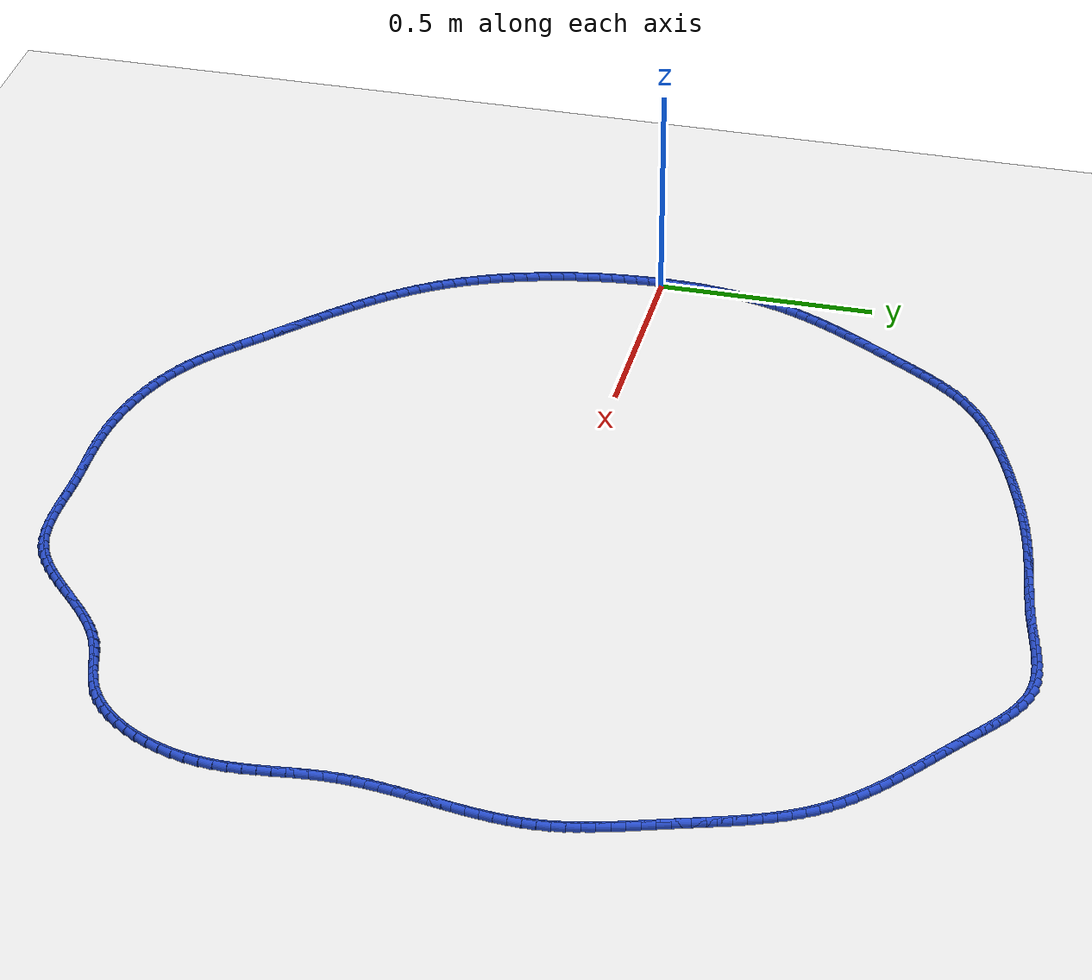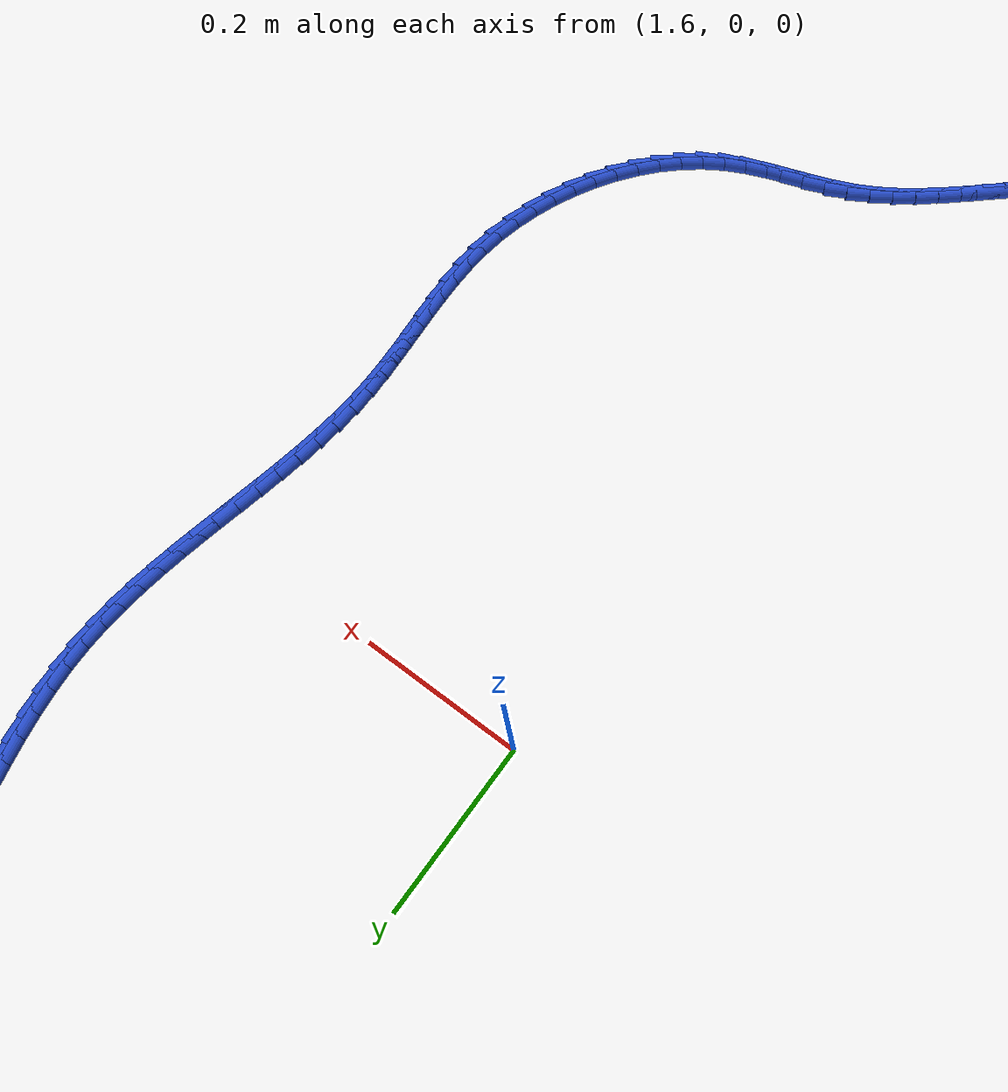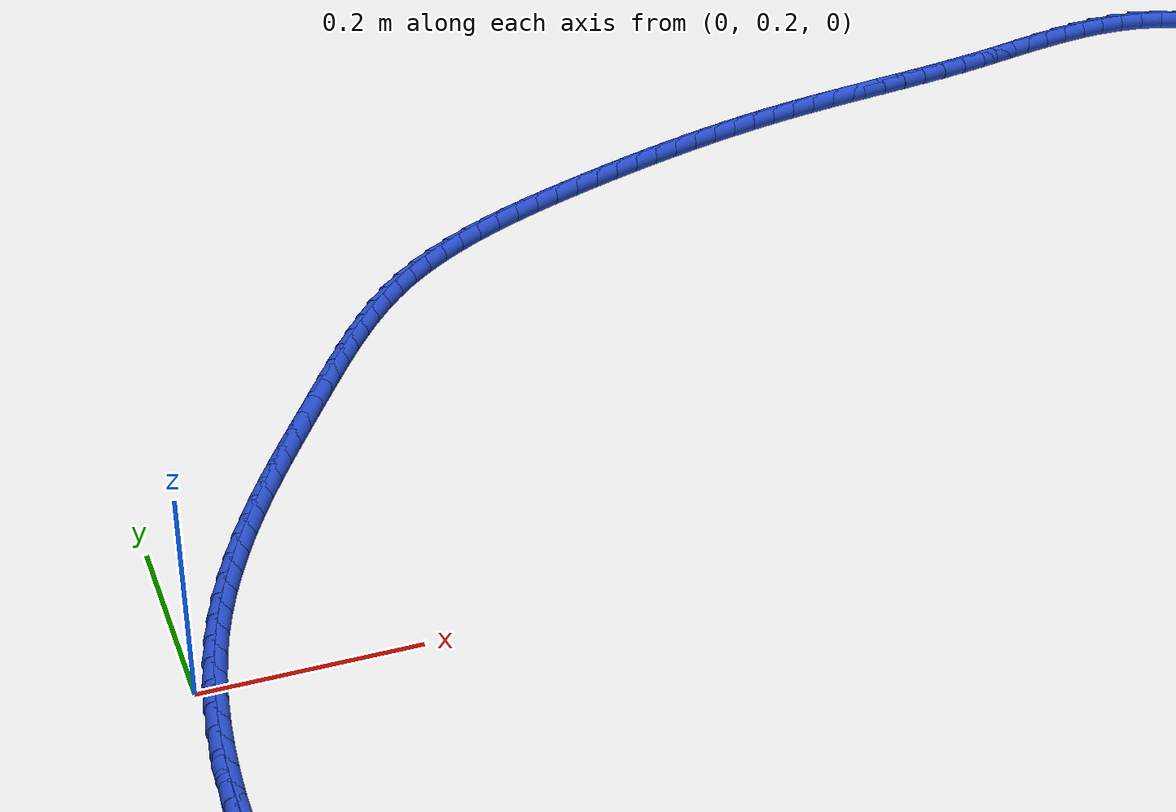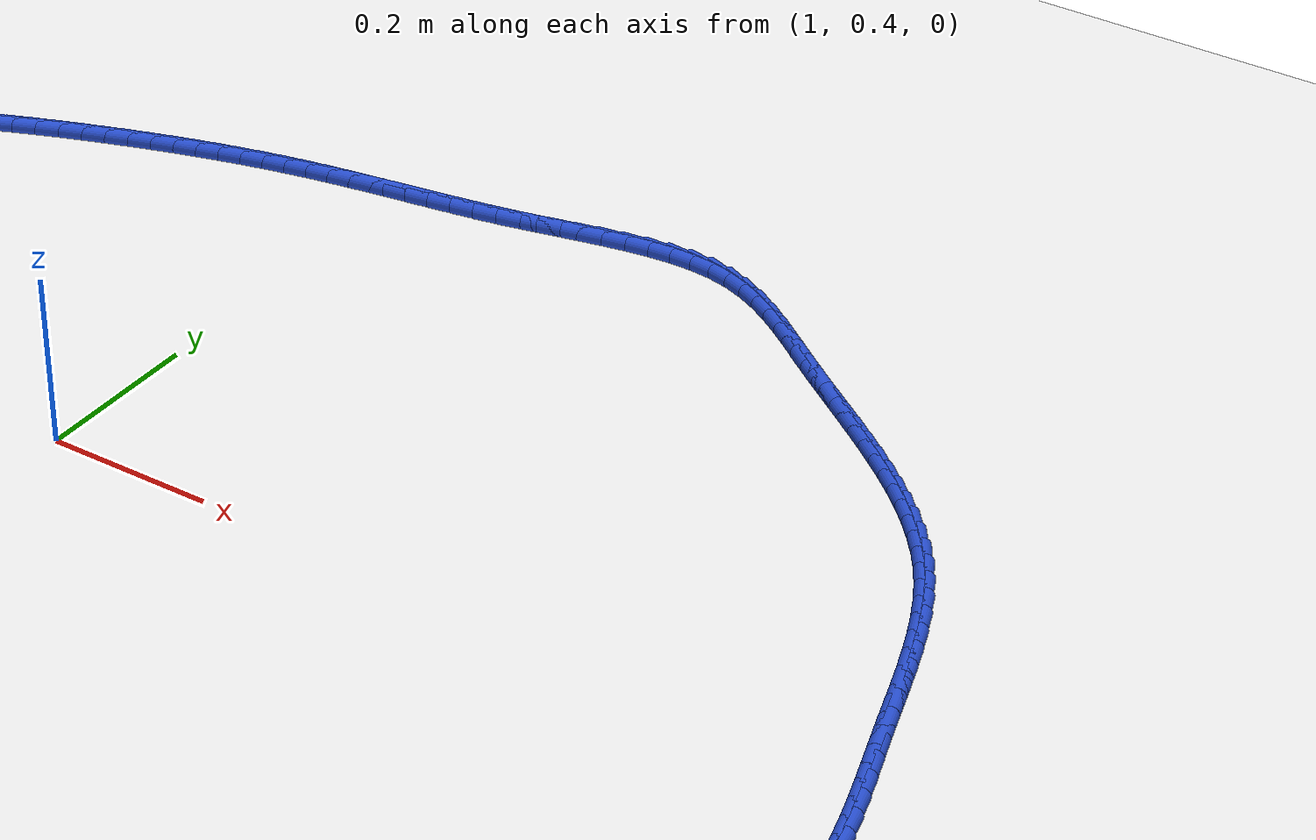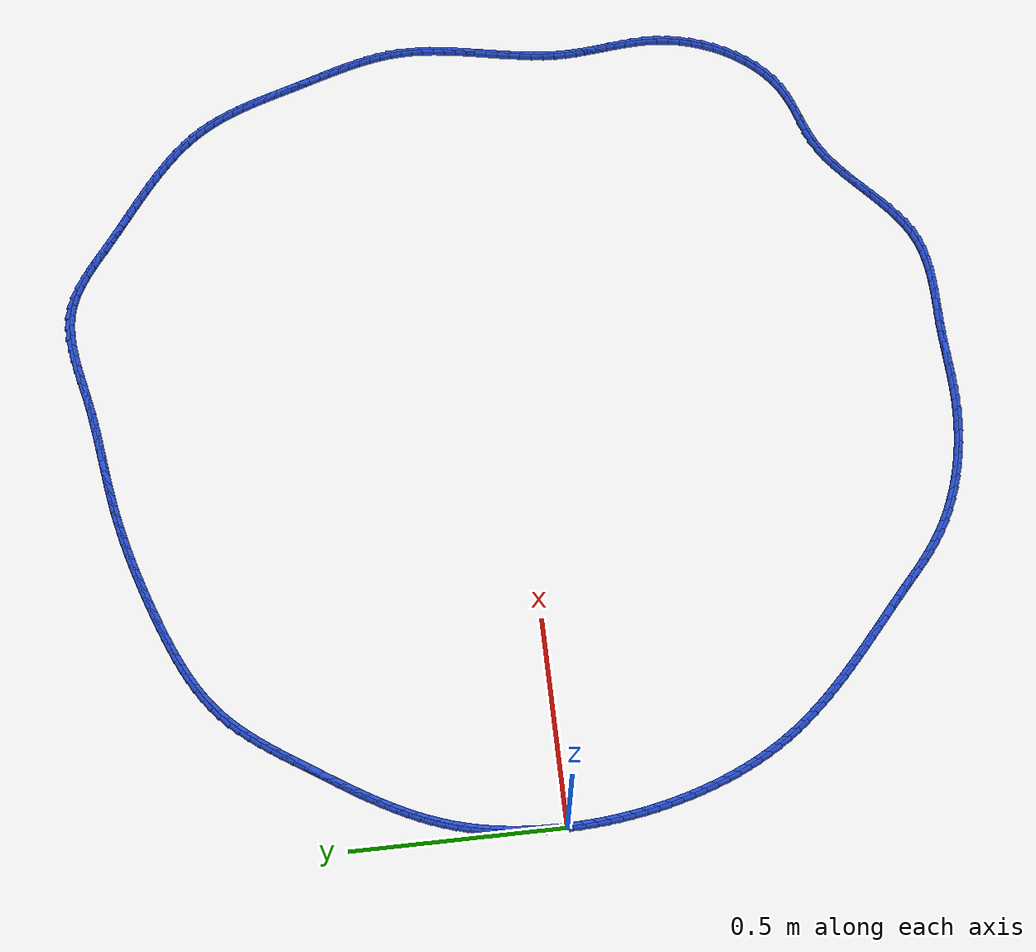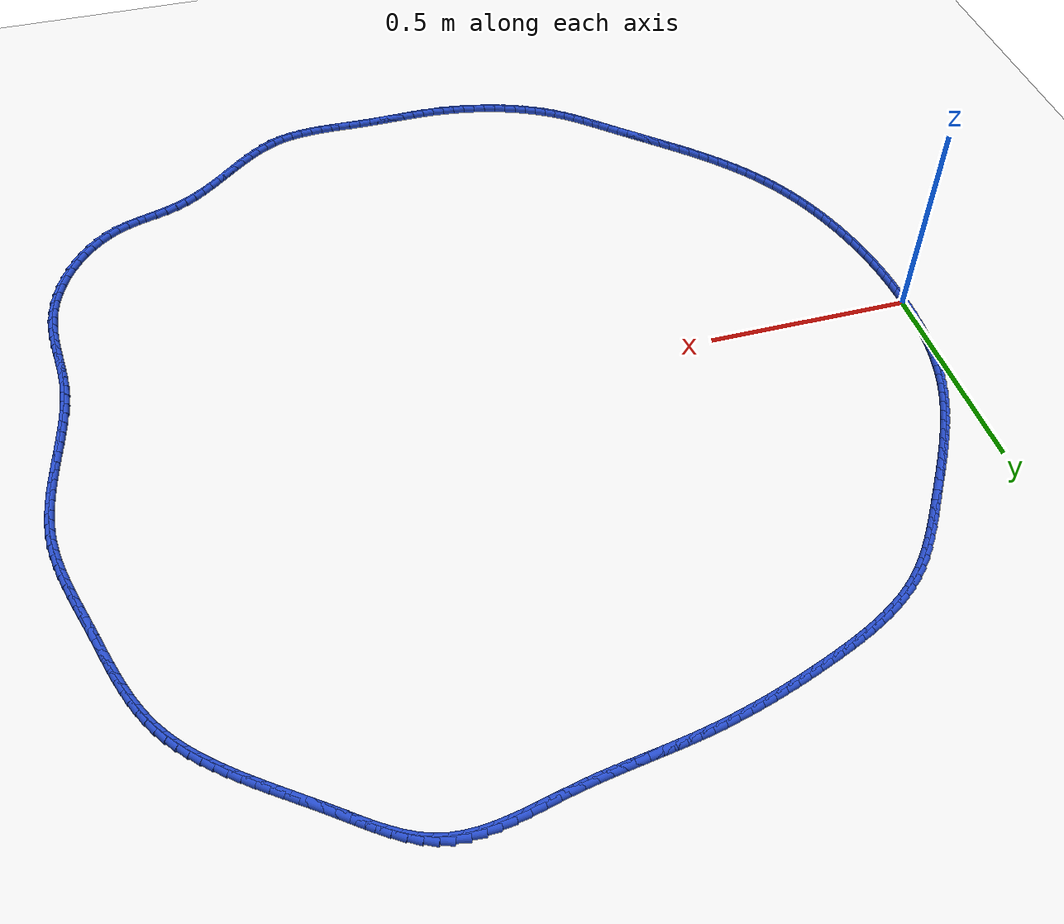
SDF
<sdf version="1.6">
 <world name="default">
  <light name="sun" type="directional">
   <pose>0 0 10 0 -0 0</pose>
   <diffuse>0.8 0.8 0.8 1</diffuse>
   <specular>0.2 0.2 0.2 1</specular>
   <attenuation>
    <range>1000</range>
    <constant>0.9</constant>
    <linear>0.01</linear>
    <quadratic>0.001</quadratic>
   </attenuation>
   <direction>-0.5 0.1 -0.9</direction>
  </light>
  <model name="ground_plane">
   <static>1</static>
   <link name="link">
    <collision name="collision">
     <geometry><plane><normal>0 0 1</normal><size>100 100</size></plane></geometry>
     <surface><friction><ode><mu>100</mu><mu2>50</mu2></ode></friction></surface>
    </collision>
    <visual name="visual">
     <cast_shadows>0</cast_shadows>
     <geometry><plane><normal>0 0 1</normal><size>100 100</size></plane></geometry>
     <material>
      <script><uri>file://media/materials/scripts/gazebo.material</uri><name>Gazebo/WhiteGlow</name></script>
     </material>
    </visual>
   </link>
  </model>
  <gravity>0 0 -9.8</gravity>
  <magnetic_field>6e-06 2.3e-05 -4.2e-05</magnetic_field>
  <atmosphere type="adiabatic"/>
  <physics name="default_physics" default="0" type="ode">
   <max_step_size>0.001</max_step_size>
   <real_time_factor>1</real_time_factor>
   <real_time_update_rate>1000</real_time_update_rate>
  </physics>
  <scene><ambient>0.4 0.4 0.4 1</ambient><background>0.7 0.7 0.7 1</background><shadows>1</shadows></scene>
  <spherical_coordinates>
   <surface_model>EARTH_WGS84</surface_model>
   <latitude_deg>0</latitude_deg>
   <longitude_deg>0</longitude_deg>
   <elevation>0</elevation>
   <heading_deg>0</heading_deg>
  </spherical_coordinates>
  <model name="line">
   <link name="link_0">
    <pose>1.3010426069826053e-18 -2.7755575615628914e-17 0.01 0 1.57 1.5690759553650164</pose>
    <collision name="collision">
     <geometry><cylinder><radius>0.01</radius><length>0.08</length></cylinder></geometry>
    </collision>
    <visual name="visual">
     <material>
      <script><name>Gazebo/Blue</name><uri>file://media/materials/scripts/gazebo.material</uri></script>
     </material>
     <geometry><cylinder><radius>0.01</radius><length>0.08</length></cylinder></geometry>
    </visual>
   </link>
   <link name="link_1">
    <pose>5.004974957747852e-05 0.0290923804773428 0.01 0 1.57 1.5415738174035163</pose>
    <collision name="collision">
     <geometry><cylinder><radius>0.01</radius><length>0.08</length></cylinder></geometry>
    </collision>
    <visual name="visual">
     <material>
      <script><name>Gazebo/Blue</name><uri>file://media/materials/scripts/gazebo.material</uri></script>
     </material>
     <geometry><cylinder><radius>0.01</radius><length>0.08</length></cylinder></geometry>
    </visual>
   </link>
   <link name="link_2">
    <pose>0.0009011808145705457 0.05820996117211494 0.01 0 1.57 1.5124217109604914</pose>
    <collision name="collision">
     <geometry><cylinder><radius>0.01</radius><length>0.08</length></cylinder></geometry>
    </collision>
    <visual name="visual">
     <material>
      <script><name>Gazebo/Blue</name><uri>file://media/materials/scripts/gazebo.material</uri></script>
     </material>
     <geometry><cylinder><radius>0.01</radius><length>0.08</length></cylinder></geometry>
    </visual>
   </link>
   <link name="link_3">
    <pose>0.0026008422577431262 0.08729332889628968 0.01 0 1.57 1.4814979170119669</pose>
    <collision name="collision">
     <geometry><cylinder><radius>0.01</radius><length>0.08</length></cylinder></geometry>
    </collision>
    <visual name="visual">
     <material>
      <script><name>Gazebo/Blue</name><uri>file://media/materials/scripts/gazebo.material</uri></script>
     </material>
     <geometry><cylinder><radius>0.01</radius><length>0.08</length></cylinder></geometry>
    </visual>
   </link>
   <link name="link_4">
    <pose>0.005196483141859143 0.11628307046184042 0.01 0 1.57 1.4486790482895981</pose>
    <collision name="collision">
     <geometry><cylinder><radius>0.01</radius><length>0.08</length></cylinder></geometry>
    </collision>
    <visual name="visual">
     <material>
      <script><name>Gazebo/Blue</name><uri>file://media/materials/scripts/gazebo.material</uri></script>
     </material>
     <geometry><cylinder><radius>0.01</radius><length>0.08</length></cylinder></geometry>
    </visual>
   </link>
   <link name="link_5">
    <pose>0.00873555252968252 0.14511977268074042 0.01 0 1.57 1.4138424131011929</pose>
    <collision name="collision">
     <geometry><cylinder><radius>0.01</radius><length>0.08</length></cylinder></geometry>
    </collision>
    <visual name="visual">
     <material>
      <script><name>Gazebo/Blue</name><uri>file://media/materials/scripts/gazebo.material</uri></script>
     </material>
     <geometry><cylinder><radius>0.01</radius><length>0.08</length></cylinder></geometry>
    </visual>
   </link>
   <link name="link_6">
    <pose>0.013265499483977186 0.17374402236496306 0.01 0 1.57 1.3768692616429017</pose>
    <collision name="collision">
     <geometry><cylinder><radius>0.01</radius><length>0.08</length></cylinder></geometry>
    </collision>
    <visual name="visual">
     <material>
      <script><name>Gazebo/Blue</name><uri>file://media/materials/scripts/gazebo.material</uri></script>
     </material>
     <geometry><cylinder><radius>0.01</radius><length>0.08</length></cylinder></geometry>
    </visual>
   </link>
   <link name="link_7">
    <pose>0.018833773067507057 0.20209640632648157 0.01 0 1.57 1.337649064226488</pose>
    <collision name="collision">
     <geometry><cylinder><radius>0.01</radius><length>0.08</length></cylinder></geometry>
    </collision>
    <visual name="visual">
     <material>
      <script><name>Gazebo/Blue</name><uri>file://media/materials/scripts/gazebo.material</uri></script>
     </material>
     <geometry><cylinder><radius>0.01</radius><length>0.08</length></cylinder></geometry>
    </visual>
   </link>
   <link name="link_8">
    <pose>0.025487822343036072 0.23011751137726943 0.01 0 1.57 1.296084943133296</pose>
    <collision name="collision">
     <geometry><cylinder><radius>0.01</radius><length>0.08</length></cylinder></geometry>
    </collision>
    <visual name="visual">
     <material>
      <script><name>Gazebo/Blue</name><uri>file://media/materials/scripts/gazebo.material</uri></script>
     </material>
     <geometry><cylinder><radius>0.01</radius><length>0.08</length></cylinder></geometry>
    </visual>
   </link>
   <link name="link_9">
    <pose>0.033275096373328136 0.25774792432929977 0.01 0 1.57 1.2522746346578566</pose>
    <collision name="collision">
     <geometry><cylinder><radius>0.01</radius><length>0.08</length></cylinder></geometry>
    </collision>
    <visual name="visual">
     <material>
      <script><name>Gazebo/Blue</name><uri>file://media/materials/scripts/gazebo.material</uri></script>
     </material>
     <geometry><cylinder><radius>0.01</radius><length>0.08</length></cylinder></geometry>
    </visual>
   </link>
   <link name="link_10">
    <pose>0.04223876512189171 0.28493118707589205 0.01 0 1.57 1.2093062880424952</pose>
    <collision name="collision">
     <geometry><cylinder><radius>0.01</radius><length>0.08</length></cylinder></geometry>
    </collision>
    <visual name="visual">
     <material>
      <script><name>Gazebo/Blue</name><uri>file://media/materials/scripts/gazebo.material</uri></script>
     </material>
     <geometry><cylinder><radius>0.01</radius><length>0.08</length></cylinder></geometry>
    </visual>
   </link>
   <link name="link_11">
    <pose>0.052346252854807825 0.31166315034550857 0.01 0 1.57 1.1699816997680739</pose>
    <collision name="collision">
     <geometry><cylinder><radius>0.01</radius><length>0.08</length></cylinder></geometry>
    </collision>
    <visual name="visual">
     <material>
      <script><name>Gazebo/Blue</name><uri>file://media/materials/scripts/gazebo.material</uri></script>
     </material>
     <geometry><cylinder><radius>0.01</radius><length>0.08</length></cylinder></geometry>
    </visual>
   </link>
   <link name="link_12">
    <pose>0.06350003275044186 0.33798451910724875 0.01 0 1.57 1.1345149713321698</pose>
    <collision name="collision">
     <geometry><cylinder><radius>0.01</radius><length>0.08</length></cylinder></geometry>
    </collision>
    <visual name="visual">
     <material>
      <script><name>Gazebo/Blue</name><uri>file://media/materials/scripts/gazebo.material</uri></script>
     </material>
     <geometry><cylinder><radius>0.01</radius><length>0.08</length></cylinder></geometry>
    </visual>
   </link>
   <link name="link_13">
    <pose>0.07560047382017349 0.36393745143616657 0.01 0 1.57 1.1029698436291127</pose>
    <collision name="collision">
     <geometry><cylinder><radius>0.01</radius><length>0.08</length></cylinder></geometry>
    </collision>
    <visual name="visual">
     <material>
      <script><name>Gazebo/Blue</name><uri>file://media/materials/scripts/gazebo.material</uri></script>
     </material>
     <geometry><cylinder><radius>0.01</radius><length>0.08</length></cylinder></geometry>
    </visual>
   </link>
   <link name="link_14">
    <pose>0.08854794507538247 0.3895641054073162 0.01 0 1.57 1.0753605912306716</pose>
    <collision name="collision">
     <geometry><cylinder><radius>0.01</radius><length>0.08</length></cylinder></geometry>
    </collision>
    <visual name="visual">
     <material>
      <script><name>Gazebo/Blue</name><uri>file://media/materials/scripts/gazebo.material</uri></script>
     </material>
     <geometry><cylinder><radius>0.01</radius><length>0.08</length></cylinder></geometry>
    </visual>
   </link>
   <link name="link_15">
    <pose>0.10224281552744846 0.414906639095752 0.01 0 1.57 1.0516665819928384</pose>
    <collision name="collision">
     <geometry><cylinder><radius>0.01</radius><length>0.08</length></cylinder></geometry>
    </collision>
    <visual name="visual">
     <material>
      <script><name>Gazebo/Blue</name><uri>file://media/materials/scripts/gazebo.material</uri></script>
     </material>
     <geometry><cylinder><radius>0.01</radius><length>0.08</length></cylinder></geometry>
    </visual>
   </link>
   <link name="link_16">
    <pose>0.11658545418775122 0.440007210576528 0.01 0 1.57 1.0318452512711922</pose>
    <collision name="collision">
     <geometry><cylinder><radius>0.01</radius><length>0.08</length></cylinder></geometry>
    </collision>
    <visual name="visual">
     <material>
      <script><name>Gazebo/Blue</name><uri>file://media/materials/scripts/gazebo.material</uri></script>
     </material>
     <geometry><cylinder><radius>0.01</radius><length>0.08</length></cylinder></geometry>
    </visual>
   </link>
   <link name="link_17">
    <pose>0.1314762300676704 0.464907977924698 0.01 0 1.57 1.015843021114739</pose>
    <collision name="collision">
     <geometry><cylinder><radius>0.01</radius><length>0.08</length></cylinder></geometry>
    </collision>
    <visual name="visual">
     <material>
      <script><name>Gazebo/Blue</name><uri>file://media/materials/scripts/gazebo.material</uri></script>
     </material>
     <geometry><cylinder><radius>0.01</radius><length>0.08</length></cylinder></geometry>
    </visual>
   </link>
   <link name="link_18">
    <pose>0.14681551217858577 0.4896510992153167 0.01 0 1.57 1.0036040465947043</pose>
    <collision name="collision">
     <geometry><cylinder><radius>0.01</radius><length>0.08</length></cylinder></geometry>
    </collision>
    <visual name="visual">
     <material>
      <script><name>Gazebo/Blue</name><uri>file://media/materials/scripts/gazebo.material</uri></script>
     </material>
     <geometry><cylinder><radius>0.01</radius><length>0.08</length></cylinder></geometry>
    </visual>
   </link>
   <link name="link_19">
    <pose>0.1625036695318769 0.5142787325234376 0.01 0 1.57 0.9950768847724868</pose>
    <collision name="collision">
     <geometry><cylinder><radius>0.01</radius><length>0.08</length></cylinder></geometry>
    </collision>
    <visual name="visual">
     <material>
      <script><name>Gazebo/Blue</name><uri>file://media/materials/scripts/gazebo.material</uri></script>
     </material>
     <geometry><cylinder><radius>0.01</radius><length>0.08</length></cylinder></geometry>
    </visual>
   </link>
   <link name="link_20">
    <pose>0.17844107113892368 0.5388330359241152 0.01 0 1.57 0.9902192827280231</pose>
    <collision name="collision">
     <geometry><cylinder><radius>0.01</radius><length>0.08</length></cylinder></geometry>
    </collision>
    <visual name="visual">
     <material>
      <script><name>Gazebo/Blue</name><uri>file://media/materials/scripts/gazebo.material</uri></script>
     </material>
     <geometry><cylinder><radius>0.01</radius><length>0.08</length></cylinder></geometry>
    </visual>
   </link>
   <link name="link_21">
    <pose>0.19452808601110572 0.5633561674924035 0.01 0 1.57 0.9889718630923737</pose>
    <collision name="collision">
     <geometry><cylinder><radius>0.01</radius><length>0.08</length></cylinder></geometry>
    </collision>
    <visual name="visual">
     <material>
      <script><name>Gazebo/Blue</name><uri>file://media/materials/scripts/gazebo.material</uri></script>
     </material>
     <geometry><cylinder><radius>0.01</radius><length>0.08</length></cylinder></geometry>
    </visual>
   </link>
   <link name="link_22">
    <pose>0.21066574416968897 0.5878897171514578 0.01 0 1.57 0.9877302254870685</pose>
    <collision name="collision">
     <geometry><cylinder><radius>0.01</radius><length>0.08</length></cylinder></geometry>
    </collision>
    <visual name="visual">
     <material>
      <script><name>Gazebo/Blue</name><uri>file://media/materials/scripts/gazebo.material</uri></script>
     </material>
     <geometry><cylinder><radius>0.01</radius><length>0.08</length></cylinder></geometry>
    </visual>
   </link>
   <link name="link_23">
    <pose>0.2268356845600121 0.6124059897589027 0.01 0 1.57 0.979488176349727</pose>
    <collision name="collision">
     <geometry><cylinder><radius>0.01</radius><length>0.08</length></cylinder></geometry>
    </collision>
    <visual name="visual">
     <material>
      <script><name>Gazebo/Blue</name><uri>file://media/materials/scripts/gazebo.material</uri></script>
     </material>
     <geometry><cylinder><radius>0.01</radius><length>0.08</length></cylinder></geometry>
    </visual>
   </link>
   <link name="link_24">
    <pose>0.2431764388729019 0.6367424375579969 0.01 0 1.57 0.9633471436574087</pose>
    <collision name="collision">
     <geometry><cylinder><radius>0.01</radius><length>0.08</length></cylinder></geometry>
    </collision>
    <visual name="visual">
     <material>
      <script><name>Gazebo/Blue</name><uri>file://media/materials/scripts/gazebo.material</uri></script>
     </material>
     <geometry><cylinder><radius>0.01</radius><length>0.08</length></cylinder></geometry>
    </visual>
   </link>
   <link name="link_25">
    <pose>0.25984461206737386 0.6607209784378912 0.01 0 1.57 0.939130410757116</pose>
    <collision name="collision">
     <geometry><cylinder><radius>0.01</radius><length>0.08</length></cylinder></geometry>
    </collision>
    <visual name="visual">
     <material>
      <script><name>Gazebo/Blue</name><uri>file://media/materials/scripts/gazebo.material</uri></script>
     </material>
     <geometry><cylinder><radius>0.01</radius><length>0.08</length></cylinder></geometry>
    </visual>
   </link>
   <link name="link_26">
    <pose>0.2769968091024434 0.6841635302877371 0.01 0 1.57 0.9066050421722204</pose>
    <collision name="collision">
     <geometry><cylinder><radius>0.01</radius><length>0.08</length></cylinder></geometry>
    </collision>
    <visual name="visual">
     <material>
      <script><name>Gazebo/Blue</name><uri>file://media/materials/scripts/gazebo.material</uri></script>
     </material>
     <geometry><cylinder><radius>0.01</radius><length>0.08</length></cylinder></geometry>
    </visual>
   </link>
   <link name="link_27">
    <pose>0.29478963493712596 0.7068920109966854 0.01 0 1.57 0.8655269465596839</pose>
    <collision name="collision">
     <geometry><cylinder><radius>0.01</radius><length>0.08</length></cylinder></geometry>
    </collision>
    <visual name="visual">
     <material>
      <script><name>Gazebo/Blue</name><uri>file://media/materials/scripts/gazebo.material</uri></script>
     </material>
     <geometry><cylinder><radius>0.01</radius><length>0.08</length></cylinder></geometry>
    </visual>
   </link>
   <link name="link_28">
    <pose>0.3133796945304369 0.7287283384538873 0.01 0 1.57 0.8157087504019891</pose>
    <collision name="collision">
     <geometry><cylinder><radius>0.01</radius><length>0.08</length></cylinder></geometry>
    </collision>
    <visual name="visual">
     <material>
      <script><name>Gazebo/Blue</name><uri>file://media/materials/scripts/gazebo.material</uri></script>
     </material>
     <geometry><cylinder><radius>0.01</radius><length>0.08</length></cylinder></geometry>
    </visual>
   </link>
   <link name="link_29">
    <pose>0.3329235928413915 0.7494944305484932 0.01 0 1.57 0.757113264613779</pose>
    <collision name="collision">
     <geometry><cylinder><radius>0.01</radius><length>0.08</length></cylinder></geometry>
    </collision>
    <visual name="visual">
     <material>
      <script><name>Gazebo/Blue</name><uri>file://media/materials/scripts/gazebo.material</uri></script>
     </material>
     <geometry><cylinder><radius>0.01</radius><length>0.08</length></cylinder></geometry>
    </visual>
   </link>
   <link name="link_30">
    <pose>0.35357793482900546 0.7690122051696548 0.01 0 1.57 0.6919606716961594</pose>
    <collision name="collision">
     <geometry><cylinder><radius>0.01</radius><length>0.08</length></cylinder></geometry>
    </collision>
    <visual name="visual">
     <material>
      <script><name>Gazebo/Blue</name><uri>file://media/materials/scripts/gazebo.material</uri></script>
     </material>
     <geometry><cylinder><radius>0.01</radius><length>0.08</length></cylinder></geometry>
    </visual>
   </link>
   <link name="link_31">
    <pose>0.37545950153100616 0.7871440961339802 0.01 0 1.57 0.6302731415467031</pose>
    <collision name="collision">
     <geometry><cylinder><radius>0.01</radius><length>0.08</length></cylinder></geometry>
    </collision>
    <visual name="visual">
     <material>
      <script><name>Gazebo/Blue</name><uri>file://media/materials/scripts/gazebo.material</uri></script>
     </material>
     <geometry><cylinder><radius>0.01</radius><length>0.08</length></cylinder></geometry>
    </visual>
   </link>
   <link name="link_32">
    <pose>0.39849308690936247 0.8039478604252274 0.01 0 1.57 0.5751460501509529</pose>
    <collision name="collision">
     <geometry><cylinder><radius>0.01</radius><length>0.08</length></cylinder></geometry>
    </collision>
    <visual name="visual">
     <material>
      <script><name>Gazebo/Blue</name><uri>file://media/materials/scripts/gazebo.material</uri></script>
     </material>
     <geometry><cylinder><radius>0.01</radius><length>0.08</length></cylinder></geometry>
    </visual>
   </link>
   <link name="link_33">
    <pose>0.4225457044708449 0.8195400395128493 0.01 0 1.57 0.5265652644455167</pose>
    <collision name="collision">
     <geometry><cylinder><radius>0.01</radius><length>0.08</length></cylinder></geometry>
    </collision>
    <visual name="visual">
     <material>
      <script><name>Gazebo/Blue</name><uri>file://media/materials/scripts/gazebo.material</uri></script>
     </material>
     <geometry><cylinder><radius>0.01</radius><length>0.08</length></cylinder></geometry>
    </visual>
   </link>
   <link name="link_34">
    <pose>0.447484356172139 0.834037186617085 0.01 0 1.57 0.4843781751000266</pose>
    <collision name="collision">
     <geometry><cylinder><radius>0.01</radius><length>0.08</length></cylinder></geometry>
    </collision>
    <visual name="visual">
     <material>
      <script><name>Gazebo/Blue</name><uri>file://media/materials/scripts/gazebo.material</uri></script>
     </material>
     <geometry><cylinder><radius>0.01</radius><length>0.08</length></cylinder></geometry>
    </visual>
   </link>
   <link name="link_35">
    <pose>0.4731760439699307 0.8475558549581744 0.01 0 1.57 0.44835717572725314</pose>
    <collision name="collision">
     <geometry><cylinder><radius>0.01</radius><length>0.08</length></cylinder></geometry>
    </collision>
    <visual name="visual">
     <material>
      <script><name>Gazebo/Blue</name><uri>file://media/materials/scripts/gazebo.material</uri></script>
     </material>
     <geometry><cylinder><radius>0.01</radius><length>0.08</length></cylinder></geometry>
    </visual>
   </link>
   <link name="link_36">
    <pose>0.49948776982090554 0.8602125977563568 0.01 0 1.57 0.4182495026088129</pose>
    <collision name="collision">
     <geometry><cylinder><radius>0.01</radius><length>0.08</length></cylinder></geometry>
    </collision>
    <visual name="visual">
     <material>
      <script><name>Gazebo/Blue</name><uri>file://media/materials/scripts/gazebo.material</uri></script>
     </material>
     <geometry><cylinder><radius>0.01</radius><length>0.08</length></cylinder></geometry>
    </visual>
   </link>
   <link name="link_37">
    <pose>0.5262865356817495 0.8721239682318719 0.01 0 1.57 0.3938142040465649</pose>
    <collision name="collision">
     <geometry><cylinder><radius>0.01</radius><length>0.08</length></cylinder></geometry>
    </collision>
    <visual name="visual">
     <material>
      <script><name>Gazebo/Blue</name><uri>file://media/materials/scripts/gazebo.material</uri></script>
     </material>
     <geometry><cylinder><radius>0.01</radius><length>0.08</length></cylinder></geometry>
    </visual>
   </link>
   <link name="link_38">
    <pose>0.5534393435091479 0.8834065196049584 0.01 0 1.57 0.37484848022260714</pose>
    <collision name="collision">
     <geometry><cylinder><radius>0.01</radius><length>0.08</length></cylinder></geometry>
    </collision>
    <visual name="visual">
     <material>
      <script><name>Gazebo/Blue</name><uri>file://media/materials/scripts/gazebo.material</uri></script>
     </material>
     <geometry><cylinder><radius>0.01</radius><length>0.08</length></cylinder></geometry>
    </visual>
   </link>
   <link name="link_39">
    <pose>0.5808131952597871 0.8941768050958566 0.01 0 1.57 0.3610011816943121</pose>
    <collision name="collision">
     <geometry><cylinder><radius>0.01</radius><length>0.08</length></cylinder></geometry>
    </collision>
    <visual name="visual">
     <material>
      <script><name>Gazebo/Blue</name><uri>file://media/materials/scripts/gazebo.material</uri></script>
     </material>
     <geometry><cylinder><radius>0.01</radius><length>0.08</length></cylinder></geometry>
    </visual>
   </link>
   <link name="link_40">
    <pose>0.6082796890626223 0.9045466785115209 0.01 0 1.57 0.3490017522980796</pose>
    <collision name="collision">
     <geometry><cylinder><radius>0.01</radius><length>0.08</length></cylinder></geometry>
    </collision>
    <visual name="visual">
     <material>
      <script><name>Gazebo/Blue</name><uri>file://media/materials/scripts/gazebo.material</uri></script>
     </material>
     <geometry><cylinder><radius>0.01</radius><length>0.08</length></cylinder></geometry>
    </visual>
   </link>
   <link name="link_41">
    <pose>0.6357820751471124 0.9145547320809587 0.01 0 1.57 0.33630322844325317</pose>
    <collision name="collision">
     <geometry><cylinder><radius>0.01</radius><length>0.08</length></cylinder></geometry>
    </collision>
    <visual name="visual">
     <material>
      <script><name>Gazebo/Blue</name><uri>file://media/materials/scripts/gazebo.material</uri></script>
     </material>
     <geometry><cylinder><radius>0.01</radius><length>0.08</length></cylinder></geometry>
    </visual>
   </link>
   <link name="link_42">
    <pose>0.6633202726406509 0.9241816162163449 0.01 0 1.57 0.32282582056405384</pose>
    <collision name="collision">
     <geometry><cylinder><radius>0.01</radius><length>0.08</length></cylinder></geometry>
    </collision>
    <visual name="visual">
     <material>
      <script><name>Gazebo/Blue</name><uri>file://media/materials/scripts/gazebo.material</uri></script>
     </material>
     <geometry><cylinder><radius>0.01</radius><length>0.08</length></cylinder></geometry>
    </visual>
   </link>
   <link name="link_43">
    <pose>0.6908957484080606 0.9334063988265403 0.01 0 1.57 0.30855931035866546</pose>
    <collision name="collision">
     <geometry><cylinder><radius>0.01</radius><length>0.08</length></cylinder></geometry>
    </collision>
    <visual name="visual">
     <material>
      <script><name>Gazebo/Blue</name><uri>file://media/materials/scripts/gazebo.material</uri></script>
     </material>
     <geometry><cylinder><radius>0.01</radius><length>0.08</length></cylinder></geometry>
    </visual>
   </link>
   <link name="link_44">
    <pose>0.7185099693141656 0.9422081478204061 0.01 0 1.57 0.2934942522518183</pose>
    <collision name="collision">
     <geometry><cylinder><radius>0.01</radius><length>0.08</length></cylinder></geometry>
    </collision>
    <visual name="visual">
     <material>
      <script><name>Gazebo/Blue</name><uri>file://media/materials/scripts/gazebo.material</uri></script>
     </material>
     <geometry><cylinder><radius>0.01</radius><length>0.08</length></cylinder></geometry>
    </visual>
   </link>
   <link name="link_45">
    <pose>0.7461644022237894 0.950565931106804 0.01 0 1.57 0.2776222474836037</pose>
    <collision name="collision">
     <geometry><cylinder><radius>0.01</radius><length>0.08</length></cylinder></geometry>
    </collision>
    <visual name="visual">
     <material>
      <script><name>Gazebo/Blue</name><uri>file://media/materials/scripts/gazebo.material</uri></script>
     </material>
     <geometry><cylinder><radius>0.01</radius><length>0.08</length></cylinder></geometry>
    </visual>
   </link>
   <link name="link_46">
    <pose>0.7738605140017553 0.958458816594595 0.01 0 1.57 0.26093624460068987</pose>
    <collision name="collision">
     <geometry><cylinder><radius>0.01</radius><length>0.08</length></cylinder></geometry>
    </collision>
    <visual name="visual">
     <material>
      <script><name>Gazebo/Blue</name><uri>file://media/materials/scripts/gazebo.material</uri></script>
     </material>
     <geometry><cylinder><radius>0.01</radius><length>0.08</length></cylinder></geometry>
    </visual>
   </link>
   <link name="link_47">
    <pose>0.8015997715128873 0.965865872192641 0.01 0 1.57 0.243430865469359</pose>
    <collision name="collision">
     <geometry><cylinder><radius>0.01</radius><length>0.08</length></cylinder></geometry>
    </collision>
    <visual name="visual">
     <material>
      <script><name>Gazebo/Blue</name><uri>file://media/materials/scripts/gazebo.material</uri></script>
     </material>
     <geometry><cylinder><radius>0.01</radius><length>0.08</length></cylinder></geometry>
    </visual>
   </link>
   <link name="link_48">
    <pose>0.8293836416220086 0.9727661658098025 0.01 0 1.57 0.22510275486886466</pose>
    <collision name="collision">
     <geometry><cylinder><radius>0.01</radius><length>0.08</length></cylinder></geometry>
    </collision>
    <visual name="visual">
     <material>
      <script><name>Gazebo/Blue</name><uri>file://media/materials/scripts/gazebo.material</uri></script>
     </material>
     <geometry><cylinder><radius>0.01</radius><length>0.08</length></cylinder></geometry>
    </visual>
   </link>
   <link name="link_49">
    <pose>0.8572135911939428 0.9791387653549414 0.01 0 1.57 0.2059509504466292</pose>
    <collision name="collision">
     <geometry><cylinder><radius>0.01</radius><length>0.08</length></cylinder></geometry>
    </collision>
    <visual name="visual">
     <material>
      <script><name>Gazebo/Blue</name><uri>file://media/materials/scripts/gazebo.material</uri></script>
     </material>
     <geometry><cylinder><radius>0.01</radius><length>0.08</length></cylinder></geometry>
    </visual>
   </link>
   <link name="link_50">
    <pose>0.8850910870935139 0.9849627387369191 0.01 0 1.57 0.18664070209297404</pose>
    <collision name="collision">
     <geometry><cylinder><radius>0.01</radius><length>0.08</length></cylinder></geometry>
    </collision>
    <visual name="visual">
     <material>
      <script><name>Gazebo/Blue</name><uri>file://media/materials/scripts/gazebo.material</uri></script>
     </material>
     <geometry><cylinder><radius>0.01</radius><length>0.08</length></cylinder></geometry>
    </visual>
   </link>
   <link name="link_51">
    <pose>0.9130198151433598 0.9902367585638872 0.01 0 1.57 0.17068896234548728</pose>
    <collision name="collision">
     <geometry><cylinder><radius>0.01</radius><length>0.08</length></cylinder></geometry>
    </collision>
    <visual name="visual">
     <material>
      <script><name>Gazebo/Blue</name><uri>file://media/materials/scripts/gazebo.material</uri></script>
     </material>
     <geometry><cylinder><radius>0.01</radius><length>0.08</length></cylinder></geometry>
    </visual>
   </link>
   <link name="link_52">
    <pose>0.9410150851031198 0.9950621960117496 0.01 0 1.57 0.15930778160910172</pose>
    <collision name="collision">
     <geometry><cylinder><radius>0.01</radius><length>0.08</length></cylinder></geometry>
    </collision>
    <visual name="visual">
     <material>
      <script><name>Gazebo/Blue</name><uri>file://media/materials/scripts/gazebo.material</uri></script>
     </material>
     <geometry><cylinder><radius>0.01</radius><length>0.08</length></cylinder></geometry>
    </visual>
   </link>
   <link name="link_53">
    <pose>0.9690960000750288 0.9995739367921072 0.01 0 1.57 0.15253468439287154</pose>
    <collision name="collision">
     <geometry><cylinder><radius>0.01</radius><length>0.08</length></cylinder></geometry>
    </collision>
    <visual name="visual">
     <material>
      <script><name>Gazebo/Blue</name><uri>file://media/materials/scripts/gazebo.material</uri></script>
     </material>
     <geometry><cylinder><radius>0.01</radius><length>0.08</length></cylinder></geometry>
    </visual>
   </link>
   <link name="link_54">
    <pose>0.9972816652687317 1.003906885235725 0.01 0 1.57 0.15036241989954485</pose>
    <collision name="collision">
     <geometry><cylinder><radius>0.01</radius><length>0.08</length></cylinder></geometry>
    </collision>
    <visual name="visual">
     <material>
      <script><name>Gazebo/Blue</name><uri>file://media/materials/scripts/gazebo.material</uri></script>
     </material>
     <geometry><cylinder><radius>0.01</radius><length>0.08</length></cylinder></geometry>
    </visual>
   </link>
   <link name="link_55">
    <pose>1.025591185893873 1.0081959456733693 0.01 0 1.57 0.15274449834497703</pose>
    <collision name="collision">
     <geometry><cylinder><radius>0.01</radius><length>0.08</length></cylinder></geometry>
    </collision>
    <visual name="visual">
     <material>
      <script><name>Gazebo/Blue</name><uri>file://media/materials/scripts/gazebo.material</uri></script>
     </material>
     <geometry><cylinder><radius>0.01</radius><length>0.08</length></cylinder></geometry>
    </visual>
   </link>
   <link name="link_56">
    <pose>1.0540436671600986 1.012576022435806 0.01 0 1.57 0.15959796919507002</pose>
    <collision name="collision">
     <geometry><cylinder><radius>0.01</radius><length>0.08</length></cylinder></geometry>
    </collision>
    <visual name="visual">
     <material>
      <script><name>Gazebo/Blue</name><uri>file://media/materials/scripts/gazebo.material</uri></script>
     </material>
     <geometry><cylinder><radius>0.01</radius><length>0.08</length></cylinder></geometry>
    </visual>
   </link>
   <link name="link_57">
    <pose>1.082658214277052 1.0171820198538 0.01 0 1.57 0.17080412431810776</pose>
    <collision name="collision">
     <geometry><cylinder><radius>0.01</radius><length>0.08</length></cylinder></geometry>
    </collision>
    <visual name="visual">
     <material>
      <script><name>Gazebo/Blue</name><uri>file://media/materials/scripts/gazebo.material</uri></script>
     </material>
     <geometry><cylinder><radius>0.01</radius><length>0.08</length></cylinder></geometry>
    </visual>
   </link>
   <link name="link_58">
    <pose>1.1114539324543788 1.0221488422581175 0.01 0 1.57 0.1862074624738569</pose>
    <collision name="collision">
     <geometry><cylinder><radius>0.01</radius><length>0.08</length></cylinder></geometry>
    </collision>
    <visual name="visual">
     <material>
      <script><name>Gazebo/Blue</name><uri>file://media/materials/scripts/gazebo.material</uri></script>
     </material>
     <geometry><cylinder><radius>0.01</radius><length>0.08</length></cylinder></geometry>
    </visual>
   </link>
   <link name="link_59">
    <pose>1.1404499269017243 1.0276113939795244 0.01 0 1.57 0.2055486253908169</pose>
    <collision name="collision">
     <geometry><cylinder><radius>0.01</radius><length>0.08</length></cylinder></geometry>
    </collision>
    <visual name="visual">
     <material>
      <script><name>Gazebo/Blue</name><uri>file://media/materials/scripts/gazebo.material</uri></script>
     </material>
     <geometry><cylinder><radius>0.01</radius><length>0.08</length></cylinder></geometry>
    </visual>
   </link>
   <link name="link_60">
    <pose>1.1696648374953547 1.0337025049223767 0.01 0 1.57 0.22237080389469602</pose>
    <collision name="collision">
     <geometry><cylinder><radius>0.01</radius><length>0.08</length></cylinder></geometry>
    </collision>
    <visual name="visual">
     <material>
      <script><name>Gazebo/Blue</name><uri>file://media/materials/scripts/gazebo.material</uri></script>
     </material>
     <geometry><cylinder><radius>0.01</radius><length>0.08</length></cylinder></geometry>
    </visual>
   </link>
   <link name="link_61">
    <pose>1.1990716973731266 1.0403516930710108 0.01 0 1.57 0.2255183421538735</pose>
    <collision name="collision">
     <geometry><cylinder><radius>0.01</radius><length>0.08</length></cylinder></geometry>
    </collision>
    <visual name="visual">
     <material>
      <script><name>Gazebo/Blue</name><uri>file://media/materials/scripts/gazebo.material</uri></script>
     </material>
     <geometry><cylinder><radius>0.01</radius><length>0.08</length></cylinder></geometry>
    </visual>
   </link>
   <link name="link_62">
    <pose>1.2285602045601212 1.0471169738122497 0.01 0 1.57 0.2139766904690584</pose>
    <collision name="collision">
     <geometry><cylinder><radius>0.01</radius><length>0.08</length></cylinder></geometry>
    </collision>
    <visual name="visual">
     <material>
      <script><name>Gazebo/Blue</name><uri>file://media/materials/scripts/gazebo.material</uri></script>
     </material>
     <geometry><cylinder><radius>0.01</radius><length>0.08</length></cylinder></geometry>
    </visual>
   </link>
   <link name="link_63">
    <pose>1.2580111753238985 1.0535167682265085 0.01 0 1.57 0.1873277203398336</pose>
    <collision name="collision">
     <geometry><cylinder><radius>0.01</radius><length>0.08</length></cylinder></geometry>
    </collision>
    <visual name="visual">
     <material>
      <script><name>Gazebo/Blue</name><uri>file://media/materials/scripts/gazebo.material</uri></script>
     </material>
     <geometry><cylinder><radius>0.01</radius><length>0.08</length></cylinder></geometry>
    </visual>
   </link>
   <link name="link_64">
    <pose>1.2873054259320185 1.0590694973942036 0.01 0 1.57 0.14455073356745138</pose>
    <collision name="collision">
     <geometry><cylinder><radius>0.01</radius><length>0.08</length></cylinder></geometry>
    </collision>
    <visual name="visual">
     <material>
      <script><name>Gazebo/Blue</name><uri>file://media/materials/scripts/gazebo.material</uri></script>
     </material>
     <geometry><cylinder><radius>0.01</radius><length>0.08</length></cylinder></geometry>
    </visual>
   </link>
   <link name="link_65">
    <pose>1.3163237726520411 1.063293582395751 0.01 0 1.57 0.08413311032034433</pose>
    <collision name="collision">
     <geometry><cylinder><radius>0.01</radius><length>0.08</length></cylinder></geometry>
    </collision>
    <visual name="visual">
     <material>
      <script><name>Gazebo/Blue</name><uri>file://media/materials/scripts/gazebo.material</uri></script>
     </material>
     <geometry><cylinder><radius>0.01</radius><length>0.08</length></cylinder></geometry>
    </visual>
   </link>
   <link name="link_66">
    <pose>1.3449470317515266 1.0657074443115666 0.01 0 1.57 0.004342352859184883</pose>
    <collision name="collision">
     <geometry><cylinder><radius>0.01</radius><length>0.08</length></cylinder></geometry>
    </collision>
    <visual name="visual">
     <material>
      <script><name>Gazebo/Blue</name><uri>file://media/materials/scripts/gazebo.material</uri></script>
     </material>
     <geometry><cylinder><radius>0.01</radius><length>0.08</length></cylinder></geometry>
    </visual>
   </link>
   <link name="link_67">
    <pose>1.3730560194980346 1.0658295042220658 0.01 0 1.57 -0.09619967052849505</pose>
    <collision name="collision">
     <geometry><cylinder><radius>0.01</radius><length>0.08</length></cylinder></geometry>
    </collision>
    <visual name="visual">
     <material>
      <script><name>Gazebo/Blue</name><uri>file://media/materials/scripts/gazebo.material</uri></script>
     </material>
     <geometry><cylinder><radius>0.01</radius><length>0.08</length></cylinder></geometry>
    </visual>
   </link>
   <link name="link_68">
    <pose>1.4005315521591255 1.063178183207665 0.01 0 1.57 -0.2174597473291746</pose>
    <collision name="collision">
     <geometry><cylinder><radius>0.01</radius><length>0.08</length></cylinder></geometry>
    </collision>
    <visual name="visual">
     <material>
      <script><name>Gazebo/Blue</name><uri>file://media/materials/scripts/gazebo.material</uri></script>
     </material>
     <geometry><cylinder><radius>0.01</radius><length>0.08</length></cylinder></geometry>
    </visual>
   </link>
   <link name="link_69">
    <pose>1.4272548723546117 1.0572735680588703 0.01 0 1.57 -0.3452900698255965</pose>
    <collision name="collision">
     <geometry><cylinder><radius>0.01</radius><length>0.08</length></cylinder></geometry>
    </collision>
    <visual name="visual">
     <material>
      <script><name>Gazebo/Blue</name><uri>file://media/materials/scripts/gazebo.material</uri></script>
     </material>
     <geometry><cylinder><radius>0.01</radius><length>0.08</length></cylinder></geometry>
    </visual>
   </link>
   <link name="link_70">
    <pose>1.4531866138608027 1.0479459178460448 0.01 0 1.57 -0.4512896890206143</pose>
    <collision name="collision">
     <geometry><cylinder><radius>0.01</radius><length>0.08</length></cylinder></geometry>
    </collision>
    <visual name="visual">
     <material>
      <script><name>Gazebo/Blue</name><uri>file://media/materials/scripts/gazebo.material</uri></script>
     </material>
     <geometry><cylinder><radius>0.01</radius><length>0.08</length></cylinder></geometry>
    </visual>
   </link>
   <link name="link_71">
    <pose>1.4784594251466248 1.0356975336116492 0.01 0 1.57 -0.5319905905998654</pose>
    <collision name="collision">
     <geometry><cylinder><radius>0.01</radius><length>0.08</length></cylinder></geometry>
    </collision>
    <visual name="visual">
     <material>
      <script><name>Gazebo/Blue</name><uri>file://media/materials/scripts/gazebo.material</uri></script>
     </material>
     <geometry><cylinder><radius>0.01</radius><length>0.08</length></cylinder></geometry>
    </visual>
   </link>
   <link name="link_72">
    <pose>1.50322845639373 1.0211186280478142 0.01 0 1.57 -0.5891059102644991</pose>
    <collision name="collision">
     <geometry><cylinder><radius>0.01</radius><length>0.08</length></cylinder></geometry>
    </collision>
    <visual name="visual">
     <material>
      <script><name>Gazebo/Blue</name><uri>file://media/materials/scripts/gazebo.material</uri></script>
     </material>
     <geometry><cylinder><radius>0.01</radius><length>0.08</length></cylinder></geometry>
    </visual>
   </link>
   <link name="link_73">
    <pose>1.5276488577837697 1.004799413846672 0.01 0 1.57 -0.6247274852756172</pose>
    <collision name="collision">
     <geometry><cylinder><radius>0.01</radius><length>0.08</length></cylinder></geometry>
    </collision>
    <visual name="visual">
     <material>
      <script><name>Gazebo/Blue</name><uri>file://media/materials/scripts/gazebo.material</uri></script>
     </material>
     <geometry><cylinder><radius>0.01</radius><length>0.08</length></cylinder></geometry>
    </visual>
   </link>
   <link name="link_74">
    <pose>1.551875779498397 0.9873301037003539 0.01 0 1.57 -0.6405244717120651</pose>
    <collision name="collision">
     <geometry><cylinder><radius>0.01</radius><length>0.08</length></cylinder></geometry>
    </collision>
    <visual name="visual">
     <material>
      <script><name>Gazebo/Blue</name><uri>file://media/materials/scripts/gazebo.material</uri></script>
     </material>
     <geometry><cylinder><radius>0.01</radius><length>0.08</length></cylinder></geometry>
    </visual>
   </link>
   <link name="link_75">
    <pose>1.5760643717192635 0.9693009103009919 0.01 0 1.57 -0.6377240859548199</pose>
    <collision name="collision">
     <geometry><cylinder><radius>0.01</radius><length>0.08</length></cylinder></geometry>
    </collision>
    <visual name="visual">
     <material>
      <script><name>Gazebo/Blue</name><uri>file://media/materials/scripts/gazebo.material</uri></script>
     </material>
     <geometry><cylinder><radius>0.01</radius><length>0.08</length></cylinder></geometry>
    </visual>
   </link>
   <link name="link_76">
    <pose>1.600366132557497 0.9512930079767797 0.01 0 1.57 -0.6269550194163164</pose>
    <collision name="collision">
     <geometry><cylinder><radius>0.01</radius><length>0.08</length></cylinder></geometry>
    </collision>
    <visual name="visual">
     <material>
      <script><name>Gazebo/Blue</name><uri>file://media/materials/scripts/gazebo.material</uri></script>
     </material>
     <geometry><cylinder><radius>0.01</radius><length>0.08</length></cylinder></geometry>
    </visual>
   </link>
   <link name="link_77">
    <pose>1.6248100373235916 0.9335843442547185 0.01 0 1.57 -0.6208900457566988</pose>
    <collision name="collision">
     <geometry><cylinder><radius>0.01</radius><length>0.08</length></cylinder></geometry>
    </collision>
    <visual name="visual">
     <material>
      <script><name>Gazebo/Blue</name><uri>file://media/materials/scripts/gazebo.material</uri></script>
     </material>
     <geometry><cylinder><radius>0.01</radius><length>0.08</length></cylinder></geometry>
    </visual>
   </link>
   <link name="link_78">
    <pose>1.6492763188886361 0.9160847499205257 0.01 0 1.57 -0.6203286178116589</pose>
    <collision name="collision">
     <geometry><cylinder><radius>0.01</radius><length>0.08</length></cylinder></geometry>
    </collision>
    <visual name="visual">
     <material>
      <script><name>Gazebo/Blue</name><uri>file://media/materials/scripts/gazebo.material</uri></script>
     </material>
     <geometry><cylinder><radius>0.01</radius><length>0.08</length></cylinder></geometry>
    </visual>
   </link>
   <link name="link_79">
    <pose>1.6736362522315382 0.898681886229206 0.01 0 1.57 -0.6253477756514012</pose>
    <collision name="collision">
     <geometry><cylinder><radius>0.01</radius><length>0.08</length></cylinder></geometry>
    </collision>
    <visual name="visual">
     <material>
      <script><name>Gazebo/Blue</name><uri>file://media/materials/scripts/gazebo.material</uri></script>
     </material>
     <geometry><cylinder><radius>0.01</radius><length>0.08</length></cylinder></geometry>
    </visual>
   </link>
   <link name="link_80">
    <pose>1.6977611123312055 0.8812634144357652 0.01 0 1.57 -0.6360697388973086</pose>
    <collision name="collision">
     <geometry><cylinder><radius>0.01</radius><length>0.08</length></cylinder></geometry>
    </collision>
    <visual name="visual">
     <material>
      <script><name>Gazebo/Blue</name><uri>file://media/materials/scripts/gazebo.material</uri></script>
     </material>
     <geometry><cylinder><radius>0.01</radius><length>0.08</length></cylinder></geometry>
    </visual>
   </link>
   <link name="link_81">
    <pose>1.7215221741665465 0.8637169957952088 0.01 0 1.57 -0.6526599198244101</pose>
    <collision name="collision">
     <geometry><cylinder><radius>0.01</radius><length>0.08</length></cylinder></geometry>
    </collision>
    <visual name="visual">
     <material>
      <script><name>Gazebo/Blue</name><uri>file://media/materials/scripts/gazebo.material</uri></script>
     </material>
     <geometry><cylinder><radius>0.01</radius><length>0.08</length></cylinder></geometry>
    </visual>
   </link>
   <link name="link_82">
    <pose>1.7447907127164677 0.8459302915625423 0.01 0 1.57 -0.6753194431379613</pose>
    <collision name="collision">
     <geometry><cylinder><radius>0.01</radius><length>0.08</length></cylinder></geometry>
    </collision>
    <visual name="visual">
     <material>
      <script><name>Gazebo/Blue</name><uri>file://media/materials/scripts/gazebo.material</uri></script>
     </material>
     <geometry><cylinder><radius>0.01</radius><length>0.08</length></cylinder></geometry>
    </visual>
   </link>
   <link name="link_83">
    <pose>1.7674380029598775 0.8277909629927702 0.01 0 1.57 -0.704270582120666</pose>
    <collision name="collision">
     <geometry><cylinder><radius>0.01</radius><length>0.08</length></cylinder></geometry>
    </collision>
    <visual name="visual">
     <material>
      <script><name>Gazebo/Blue</name><uri>file://media/materials/scripts/gazebo.material</uri></script>
     </material>
     <geometry><cylinder><radius>0.01</radius><length>0.08</length></cylinder></geometry>
    </visual>
   </link>
   <link name="link_84">
    <pose>1.7893353198756836 0.809186671340899 0.01 0 1.57 -0.7397330313398277</pose>
    <collision name="collision">
     <geometry><cylinder><radius>0.01</radius><length>0.08</length></cylinder></geometry>
    </collision>
    <visual name="visual">
     <material>
      <script><name>Gazebo/Blue</name><uri>file://media/materials/scripts/gazebo.material</uri></script>
     </material>
     <geometry><cylinder><radius>0.01</radius><length>0.08</length></cylinder></geometry>
    </visual>
   </link>
   <link name="link_85">
    <pose>1.8103539384427936 0.7900050778619335 0.01 0 1.57 -0.7818888342430856</pose>
    <collision name="collision">
     <geometry><cylinder><radius>0.01</radius><length>0.08</length></cylinder></geometry>
    </collision>
    <visual name="visual">
     <material>
      <script><name>Gazebo/Blue</name><uri>file://media/materials/scripts/gazebo.material</uri></script>
     </material>
     <geometry><cylinder><radius>0.01</radius><length>0.08</length></cylinder></geometry>
    </visual>
   </link>
   <link name="link_86">
    <pose>1.830365133640115 0.7701338438108795 0.01 0 1.57 -0.8308345231119459</pose>
    <collision name="collision">
     <geometry><cylinder><radius>0.01</radius><length>0.08</length></cylinder></geometry>
    </collision>
    <visual name="visual">
     <material>
      <script><name>Gazebo/Blue</name><uri>file://media/materials/scripts/gazebo.material</uri></script>
     </material>
     <geometry><cylinder><radius>0.01</radius><length>0.08</length></cylinder></geometry>
    </visual>
   </link>
   <link name="link_87">
    <pose>1.8492401804465555 0.7494606304427421 0.01 0 1.57 -0.8865212134596853</pose>
    <collision name="collision">
     <geometry><cylinder><radius>0.01</radius><length>0.08</length></cylinder></geometry>
    </collision>
    <visual name="visual">
     <material>
      <script><name>Gazebo/Blue</name><uri>file://media/materials/scripts/gazebo.material</uri></script>
     </material>
     <geometry><cylinder><radius>0.01</radius><length>0.08</length></cylinder></geometry>
    </visual>
   </link>
   <link name="link_88">
    <pose>1.866850353841023 0.7278730990125264 0.01 0 1.57 -0.948687541981576</pose>
    <collision name="collision">
     <geometry><cylinder><radius>0.01</radius><length>0.08</length></cylinder></geometry>
    </collision>
    <visual name="visual">
     <material>
      <script><name>Gazebo/Blue</name><uri>file://media/materials/scripts/gazebo.material</uri></script>
     </material>
     <geometry><cylinder><radius>0.01</radius><length>0.08</length></cylinder></geometry>
    </visual>
   </link>
   <link name="link_89">
    <pose>1.883066928802426 0.7052589107752386 0.01 0 1.57 -1.0153926227673609</pose>
    <collision name="collision">
     <geometry><cylinder><radius>0.01</radius><length>0.08</length></cylinder></geometry>
    </collision>
    <visual name="visual">
     <material>
      <script><name>Gazebo/Blue</name><uri>file://media/materials/scripts/gazebo.material</uri></script>
     </material>
     <geometry><cylinder><radius>0.01</radius><length>0.08</length></cylinder></geometry>
    </visual>
   </link>
   <link name="link_90">
    <pose>1.8977922448586817 0.6815300228409591 0.01 0 1.57 -1.0767446248066326</pose>
    <collision name="collision">
     <geometry><cylinder><radius>0.01</radius><length>0.08</length></cylinder></geometry>
    </collision>
    <visual name="visual">
     <material>
      <script><name>Gazebo/Blue</name><uri>file://media/materials/scripts/gazebo.material</uri></script>
     </material>
     <geometry><cylinder><radius>0.01</radius><length>0.08</length></cylinder></geometry>
    </visual>
   </link>
   <link name="link_91">
    <pose>1.911134007705103 0.6567590109928068 0.01 0 1.57 -1.1288276370921122</pose>
    <collision name="collision">
     <geometry><cylinder><radius>0.01</radius><length>0.08</length></cylinder></geometry>
    </collision>
    <visual name="visual">
     <material>
      <script><name>Gazebo/Blue</name><uri>file://media/materials/scripts/gazebo.material</uri></script>
     </material>
     <geometry><cylinder><radius>0.01</radius><length>0.08</length></cylinder></geometry>
    </visual>
   </link>
   <link name="link_92">
    <pose>1.9232832778422686 0.6310836435350562 0.01 0 1.57 -1.1718017173528272</pose>
    <collision name="collision">
     <geometry><cylinder><radius>0.01</radius><length>0.08</length></cylinder></geometry>
    </collision>
    <visual name="visual">
     <material>
      <script><name>Gazebo/Blue</name><uri>file://media/materials/scripts/gazebo.material</uri></script>
     </material>
     <geometry><cylinder><radius>0.01</radius><length>0.08</length></cylinder></geometry>
    </visual>
   </link>
   <link name="link_93">
    <pose>1.9344313548851955 0.6046418757854741 0.01 0 1.57 -1.2059878715627956</pose>
    <collision name="collision">
     <geometry><cylinder><radius>0.01</radius><length>0.08</length></cylinder></geometry>
    </collision>
    <visual name="visual">
     <material>
      <script><name>Gazebo/Blue</name><uri>file://media/materials/scripts/gazebo.material</uri></script>
     </material>
     <geometry><cylinder><radius>0.01</radius><length>0.08</length></cylinder></geometry>
    </visual>
   </link>
   <link name="link_94">
    <pose>1.9447695384489014 0.5775716630618266 0.01 0 1.57 -1.2317527196773816</pose>
    <collision name="collision">
     <geometry><cylinder><radius>0.01</radius><length>0.08</length></cylinder></geometry>
    </collision>
    <visual name="visual">
     <material>
      <script><name>Gazebo/Blue</name><uri>file://media/materials/scripts/gazebo.material</uri></script>
     </material>
     <geometry><cylinder><radius>0.01</radius><length>0.08</length></cylinder></geometry>
    </visual>
   </link>
   <link name="link_95">
    <pose>1.9544891281484031 0.5500109606818812 0.01 0 1.57 -1.2494365020771696</pose>
    <collision name="collision">
     <geometry><cylinder><radius>0.01</radius><length>0.08</length></cylinder></geometry>
    </collision>
    <visual name="visual">
     <material>
      <script><name>Gazebo/Blue</name><uri>file://media/materials/scripts/gazebo.material</uri></script>
     </material>
     <geometry><cylinder><radius>0.01</radius><length>0.08</length></cylinder></geometry>
    </visual>
   </link>
   <link name="link_96">
    <pose>1.9637814235987194 0.5220977239634033 0.01 0 1.57 -1.259307782410658</pose>
    <collision name="collision">
     <geometry><cylinder><radius>0.01</radius><length>0.08</length></cylinder></geometry>
    </collision>
    <visual name="visual">
     <material>
      <script><name>Gazebo/Blue</name><uri>file://media/materials/scripts/gazebo.material</uri></script>
     </material>
     <geometry><cylinder><radius>0.01</radius><length>0.08</length></cylinder></geometry>
    </visual>
   </link>
   <link name="link_97">
    <pose>1.9728377244148665 0.49396990822416054 0.01 0 1.57 -1.2615377580723661</pose>
    <collision name="collision">
     <geometry><cylinder><radius>0.01</radius><length>0.08</length></cylinder></geometry>
    </collision>
    <visual name="visual">
     <material>
      <script><name>Gazebo/Blue</name><uri>file://media/materials/scripts/gazebo.material</uri></script>
     </material>
     <geometry><cylinder><radius>0.01</radius><length>0.08</length></cylinder></geometry>
    </visual>
   </link>
   <link name="link_98">
    <pose>1.981849330211863 0.46576546878191916 0.01 0 1.57 -1.256643544453208</pose>
    <collision name="collision">
     <geometry><cylinder><radius>0.01</radius><length>0.08</length></cylinder></geometry>
    </collision>
    <visual name="visual">
     <material>
      <script><name>Gazebo/Blue</name><uri>file://media/materials/scripts/gazebo.material</uri></script>
     </material>
     <geometry><cylinder><radius>0.01</radius><length>0.08</length></cylinder></geometry>
    </visual>
   </link>
   <link name="link_99">
    <pose>1.9909949997241907 0.43761737136599266 0.01 0 1.57 -1.2523994971616854</pose>
    <collision name="collision">
     <geometry><cylinder><radius>0.01</radius><length>0.08</length></cylinder></geometry>
    </collision>
    <visual name="visual">
     <material>
      <script><name>Gazebo/Blue</name><uri>file://media/materials/scripts/gazebo.material</uri></script>
     </material>
     <geometry><cylinder><radius>0.01</radius><length>0.08</length></cylinder></geometry>
    </visual>
   </link>
   <link name="link_100">
    <pose>2.0002386961877208 0.4095731219059218 0.01 0 1.57 -1.2553770026803892</pose>
    <collision name="collision">
     <geometry><cylinder><radius>0.01</radius><length>0.08</length></cylinder></geometry>
    </collision>
    <visual name="visual">
     <material>
      <script><name>Gazebo/Blue</name><uri>file://media/materials/scripts/gazebo.material</uri></script>
     </material>
     <geometry><cylinder><radius>0.01</radius><length>0.08</length></cylinder></geometry>
    </visual>
   </link>
   <link name="link_101">
    <pose>2.0093639463786253 0.38160843682067647 0.01 0 1.57 -1.2658779330798793</pose>
    <collision name="collision">
     <geometry><cylinder><radius>0.01</radius><length>0.08</length></cylinder></geometry>
    </collision>
    <visual name="visual">
     <material>
      <script><name>Gazebo/Blue</name><uri>file://media/materials/scripts/gazebo.material</uri></script>
     </material>
     <geometry><cylinder><radius>0.01</radius><length>0.08</length></cylinder></geometry>
    </visual>
   </link>
   <link name="link_102">
    <pose>2.0181486735167526 0.3536968030653678 0.01 0 1.57 -1.284064147736876</pose>
    <collision name="collision">
     <geometry><cylinder><radius>0.01</radius><length>0.08</length></cylinder></geometry>
    </collision>
    <visual name="visual">
     <material>
      <script><name>Gazebo/Blue</name><uri>file://media/materials/scripts/gazebo.material</uri></script>
     </material>
     <geometry><cylinder><radius>0.01</radius><length>0.08</length></cylinder></geometry>
    </visual>
   </link>
   <link name="link_103">
    <pose>2.026370800821951 0.32581170759510536 0.01 0 1.57 -1.3101459925883594</pose>
    <collision name="collision">
     <geometry><cylinder><radius>0.01</radius><length>0.08</length></cylinder></geometry>
    </collision>
    <visual name="visual">
     <material>
      <script><name>Gazebo/Blue</name><uri>file://media/materials/scripts/gazebo.material</uri></script>
     </material>
     <geometry><cylinder><radius>0.01</radius><length>0.08</length></cylinder></geometry>
    </visual>
   </link>
   <link name="link_104">
    <pose>2.0338082515140687 0.2979266373650005 0.01 0 1.57 -1.3443523444464098</pose>
    <collision name="collision">
     <geometry><cylinder><radius>0.01</radius><length>0.08</length></cylinder></geometry>
    </collision>
    <visual name="visual">
     <material>
      <script><name>Gazebo/Blue</name><uri>file://media/materials/scripts/gazebo.material</uri></script>
     </material>
     <geometry><cylinder><radius>0.01</radius><length>0.08</length></cylinder></geometry>
    </visual>
   </link>
   <link name="link_105">
    <pose>2.040238948812955 0.2700150793301631 0.01 0 1.57 -1.3868819554934098</pose>
    <collision name="collision">
     <geometry><cylinder><radius>0.01</radius><length>0.08</length></cylinder></geometry>
    </collision>
    <visual name="visual">
     <material>
      <script><name>Gazebo/Blue</name><uri>file://media/materials/scripts/gazebo.material</uri></script>
     </material>
     <geometry><cylinder><radius>0.01</radius><length>0.08</length></cylinder></geometry>
    </visual>
   </link>
   <link name="link_106">
    <pose>2.0454408159384574 0.24205052044570427 0.01 0 1.57 -1.4378331358386085</pose>
    <collision name="collision">
     <geometry><cylinder><radius>0.01</radius><length>0.08</length></cylinder></geometry>
    </collision>
    <visual name="visual">
     <material>
      <script><name>Gazebo/Blue</name><uri>file://media/materials/scripts/gazebo.material</uri></script>
     </material>
     <geometry><cylinder><radius>0.01</radius><length>0.08</length></cylinder></geometry>
    </visual>
   </link>
   <link name="link_107">
    <pose>2.0491917761104257 0.21400644766673418 0.01 0 1.57 -1.4970224020601024</pose>
    <collision name="collision">
     <geometry><cylinder><radius>0.01</radius><length>0.08</length></cylinder></geometry>
    </collision>
    <visual name="visual">
     <material>
      <script><name>Gazebo/Blue</name><uri>file://media/materials/scripts/gazebo.material</uri></script>
     </material>
     <geometry><cylinder><radius>0.01</radius><length>0.08</length></cylinder></geometry>
    </visual>
   </link>
   <link name="link_108">
    <pose>2.051272279438466 0.1858565624368356 0.01 0 1.57 -1.558250301588326</pose>
    <collision name="collision">
     <geometry><cylinder><radius>0.01</radius><length>0.08</length></cylinder></geometry>
    </collision>
    <visual name="visual">
     <material>
      <script><name>Gazebo/Blue</name><uri>file://media/materials/scripts/gazebo.material</uri></script>
     </material>
     <geometry><cylinder><radius>0.01</radius><length>0.08</length></cylinder></geometry>
    </visual>
   </link>
   <link name="link_109">
    <pose>2.051626949850312 0.15758850166763197 0.01 0 1.57 1.5297791505027574</pose>
    <collision name="collision">
     <geometry><cylinder><radius>0.01</radius><length>0.08</length></cylinder></geometry>
    </collision>
    <visual name="visual">
     <material>
      <script><name>Gazebo/Blue</name><uri>file://media/materials/scripts/gazebo.material</uri></script>
     </material>
     <geometry><cylinder><radius>0.01</radius><length>0.08</length></cylinder></geometry>
    </visual>
   </link>
   <link name="link_110">
    <pose>2.0504623783983593 0.12921213866955097 0.01 0 1.57 1.48482867673259</pose>
    <collision name="collision">
     <geometry><cylinder><radius>0.01</radius><length>0.08</length></cylinder></geometry>
    </collision>
    <visual name="visual">
     <material>
      <script><name>Gazebo/Blue</name><uri>file://media/materials/scripts/gazebo.material</uri></script>
     </material>
     <geometry><cylinder><radius>0.01</radius><length>0.08</length></cylinder></geometry>
    </visual>
   </link>
   <link name="link_111">
    <pose>2.048008590621108 0.10073933592849338 0.01 0 1.57 1.4483965288731824</pose>
    <collision name="collision">
     <geometry><cylinder><radius>0.01</radius><length>0.08</length></cylinder></geometry>
    </collision>
    <visual name="visual">
     <material>
      <script><name>Gazebo/Blue</name><uri>file://media/materials/scripts/gazebo.material</uri></script>
     </material>
     <geometry><cylinder><radius>0.01</radius><length>0.08</length></cylinder></geometry>
    </visual>
   </link>
   <link name="link_112">
    <pose>2.0444956120570557 0.07218195593035845 0.01 0 1.57 1.4202797654180324</pose>
    <collision name="collision">
     <geometry><cylinder><radius>0.01</radius><length>0.08</length></cylinder></geometry>
    </collision>
    <visual name="visual">
     <material>
      <script><name>Gazebo/Blue</name><uri>file://media/materials/scripts/gazebo.material</uri></script>
     </material>
     <geometry><cylinder><radius>0.01</radius><length>0.08</length></cylinder></geometry>
    </visual>
   </link>
   <link name="link_113">
    <pose>2.040153468244703 0.04355186116104706 0.01 0 1.57 1.4002449662135965</pose>
    <collision name="collision">
     <geometry><cylinder><radius>0.01</radius><length>0.08</length></cylinder></geometry>
    </collision>
    <visual name="visual">
     <material>
      <script><name>Gazebo/Blue</name><uri>file://media/materials/scripts/gazebo.material</uri></script>
     </material>
     <geometry><cylinder><radius>0.01</radius><length>0.08</length></cylinder></geometry>
    </visual>
   </link>
   <link name="link_114">
    <pose>2.0352121847225475 0.014860914106458439 0.01 0 1.57 1.3880829356934166</pose>
    <collision name="collision">
     <geometry><cylinder><radius>0.01</radius><length>0.08</length></cylinder></geometry>
    </collision>
    <visual name="visual">
     <material>
      <script><name>Gazebo/Blue</name><uri>file://media/materials/scripts/gazebo.material</uri></script>
     </material>
     <geometry><cylinder><radius>0.01</radius><length>0.08</length></cylinder></geometry>
    </visual>
   </link>
   <link name="link_115">
    <pose>2.0299017870290896 -0.013879022747506641 0.01 0 1.57 1.3836433826684016</pose>
    <collision name="collision">
     <geometry><cylinder><radius>0.01</radius><length>0.08</length></cylinder></geometry>
    </collision>
    <visual name="visual">
     <material>
      <script><name>Gazebo/Blue</name><uri>file://media/materials/scripts/gazebo.material</uri></script>
     </material>
     <geometry><cylinder><radius>0.01</radius><length>0.08</length></cylinder></geometry>
    </visual>
   </link>
   <link name="link_116">
    <pose>2.0244523007028263 -0.042656086914948474 0.01 0 1.57 1.3868536560392821</pose>
    <collision name="collision">
     <geometry><cylinder><radius>0.01</radius><length>0.08</length></cylinder></geometry>
    </collision>
    <visual name="visual">
     <material>
      <script><name>Gazebo/Blue</name><uri>file://media/materials/scripts/gazebo.material</uri></script>
     </material>
     <geometry><cylinder><radius>0.01</radius><length>0.08</length></cylinder></geometry>
    </visual>
   </link>
   <link name="link_117">
    <pose>2.0190937512822593 -0.07145841590996778 0.01 0 1.57 1.397724615749897</pose>
    <collision name="collision">
     <geometry><cylinder><radius>0.01</radius><length>0.08</length></cylinder></geometry>
    </collision>
    <visual name="visual">
     <material>
      <script><name>Gazebo/Blue</name><uri>file://media/materials/scripts/gazebo.material</uri></script>
     </material>
     <geometry><cylinder><radius>0.01</radius><length>0.08</length></cylinder></geometry>
    </visual>
   </link>
   <link name="link_118">
    <pose>2.0140561643058845 -0.10027414724666303 0.01 0 1.57 1.4163449966087462</pose>
    <collision name="collision">
     <geometry><cylinder><radius>0.01</radius><length>0.08</length></cylinder></geometry>
    </collision>
    <visual name="visual">
     <material>
      <script><name>Gazebo/Blue</name><uri>file://media/materials/scripts/gazebo.material</uri></script>
     </material>
     <geometry><cylinder><radius>0.01</radius><length>0.08</length></cylinder></geometry>
    </visual>
   </link>
   <link name="link_119">
    <pose>2.009569565312203 -0.12909141843913496 0.01 0 1.57 1.4428637466507135</pose>
    <collision name="collision">
     <geometry><cylinder><radius>0.01</radius><length>0.08</length></cylinder></geometry>
    </collision>
    <visual name="visual">
     <material>
      <script><name>Gazebo/Blue</name><uri>file://media/materials/scripts/gazebo.material</uri></script>
     </material>
     <geometry><cylinder><radius>0.01</radius><length>0.08</length></cylinder></geometry>
    </visual>
   </link>
   <link name="link_120">
    <pose>2.0058639798397135 -0.15789836700148346 0.01 0 1.57 1.4774581656034034</pose>
    <collision name="collision">
     <geometry><cylinder><radius>0.01</radius><length>0.08</length></cylinder></geometry>
    </collision>
    <visual name="visual">
     <material>
      <script><name>Gazebo/Blue</name><uri>file://media/materials/scripts/gazebo.material</uri></script>
     </material>
     <geometry><cylinder><radius>0.01</radius><length>0.08</length></cylinder></geometry>
    </visual>
   </link>
   <link name="link_121">
    <pose>2.0031694334269146 -0.1866831304478086 0.01 0 1.57 1.520284699104089</pose>
    <collision name="collision">
     <geometry><cylinder><radius>0.01</radius><length>0.08</length></cylinder></geometry>
    </collision>
    <visual name="visual">
     <material>
      <script><name>Gazebo/Blue</name><uri>file://media/materials/scripts/gazebo.material</uri></script>
     </material>
     <geometry><cylinder><radius>0.01</radius><length>0.08</length></cylinder></geometry>
    </visual>
   </link>
   <link name="link_122">
    <pose>2.0017159516123044 -0.21543384629221096 0.01 0 1.57 -1.5704730454342877</pose>
    <collision name="collision">
     <geometry><cylinder><radius>0.01</radius><length>0.08</length></cylinder></geometry>
    </collision>
    <visual name="visual">
     <material>
      <script><name>Gazebo/Blue</name><uri>file://media/materials/scripts/gazebo.material</uri></script>
     </material>
     <geometry><cylinder><radius>0.01</radius><length>0.08</length></cylinder></geometry>
    </visual>
   </link>
   <link name="link_123">
    <pose>2.001725231491692 -0.24413911728844442 0.01 0 1.57 -1.5218194374203236</pose>
    <collision name="collision">
     <geometry><cylinder><radius>0.01</radius><length>0.08</length></cylinder></geometry>
    </collision>
    <visual name="visual">
     <material>
      <script><name>Gazebo/Blue</name><uri>file://media/materials/scripts/gazebo.material</uri></script>
     </material>
     <geometry><cylinder><radius>0.01</radius><length>0.08</length></cylinder></geometry>
    </visual>
   </link>
   <link name="link_124">
    <pose>2.0031302559322484 -0.2728036742124189 0.01 0 1.57 -1.487986631301118</pose>
    <collision name="collision">
     <geometry><cylinder><radius>0.01</radius><length>0.08</length></cylinder></geometry>
    </collision>
    <visual name="visual">
     <material>
      <script><name>Gazebo/Blue</name><uri>file://media/materials/scripts/gazebo.material</uri></script>
     </material>
     <geometry><cylinder><radius>0.01</radius><length>0.08</length></cylinder></geometry>
    </visual>
   </link>
   <link name="link_125">
    <pose>2.0055080636662 -0.30145213142846533 0.01 0 1.57 -1.4697510879479838</pose>
    <collision name="collision">
     <geometry><cylinder><radius>0.01</radius><length>0.08</length></cylinder></geometry>
    </collision>
    <visual name="visual">
     <material>
      <script><name>Gazebo/Blue</name><uri>file://media/materials/scripts/gazebo.material</uri></script>
     </material>
     <geometry><cylinder><radius>0.01</radius><length>0.08</length></cylinder></geometry>
    </visual>
   </link>
   <link name="link_126">
    <pose>2.0084137340229615 -0.3301103299870294 0.01 0 1.57 -1.4670151294423626</pose>
    <collision name="collision">
     <geometry><cylinder><radius>0.01</radius><length>0.08</length></cylinder></geometry>
    </collision>
    <visual name="visual">
     <material>
      <script><name>Gazebo/Blue</name><uri>file://media/materials/scripts/gazebo.material</uri></script>
     </material>
     <geometry><cylinder><radius>0.01</radius><length>0.08</length></cylinder></geometry>
    </visual>
   </link>
   <link name="link_127">
    <pose>2.0114023463319435 -0.3588041109385545 0.01 0 1.57 -1.479704484568105</pose>
    <collision name="collision">
     <geometry><cylinder><radius>0.01</radius><length>0.08</length></cylinder></geometry>
    </collision>
    <visual name="visual">
     <material>
      <script><name>Gazebo/Blue</name><uri>file://media/materials/scripts/gazebo.material</uri></script>
     </material>
     <geometry><cylinder><radius>0.01</radius><length>0.08</length></cylinder></geometry>
    </visual>
   </link>
   <link name="link_128">
    <pose>2.0140289799225597 -0.3875593153334863 0.01 0 1.57 -1.5077876640976542</pose>
    <collision name="collision">
     <geometry><cylinder><radius>0.01</radius><length>0.08</length></cylinder></geometry>
    </collision>
    <visual name="visual">
     <material>
      <script><name>Gazebo/Blue</name><uri>file://media/materials/scripts/gazebo.material</uri></script>
     </material>
     <geometry><cylinder><radius>0.01</radius><length>0.08</length></cylinder></geometry>
    </visual>
   </link>
   <link name="link_129">
    <pose>2.015848714124221 -0.4164017842222695 0.01 0 1.57 -1.5511855489715893</pose>
    <collision name="collision">
     <geometry><cylinder><radius>0.01</radius><length>0.08</length></cylinder></geometry>
    </collision>
    <visual name="visual">
     <material>
      <script><name>Gazebo/Blue</name><uri>file://media/materials/scripts/gazebo.material</uri></script>
     </material>
     <geometry><cylinder><radius>0.01</radius><length>0.08</length></cylinder></geometry>
    </visual>
   </link>
   <link name="link_130">
    <pose>2.0164166282663416 -0.44535735865534903 0.01 0 1.57 1.5320171807587788</pose>
    <collision name="collision">
     <geometry><cylinder><radius>0.01</radius><length>0.08</length></cylinder></geometry>
    </collision>
    <visual name="visual">
     <material>
      <script><name>Gazebo/Blue</name><uri>file://media/materials/scripts/gazebo.material</uri></script>
     </material>
     <geometry><cylinder><radius>0.01</radius><length>0.08</length></cylinder></geometry>
    </visual>
   </link>
   <link name="link_131">
    <pose>2.0152878016783333 -0.4744518796831706 0.01 0 1.57 1.4596204361337703</pose>
    <collision name="collision">
     <geometry><cylinder><radius>0.01</radius><length>0.08</length></cylinder></geometry>
    </collision>
    <visual name="visual">
     <material>
      <script><name>Gazebo/Blue</name><uri>file://media/materials/scripts/gazebo.material</uri></script>
     </material>
     <geometry><cylinder><radius>0.01</radius><length>0.08</length></cylinder></geometry>
    </visual>
   </link>
   <link name="link_132">
    <pose>2.0120216745602826 -0.5037087578428138 0.01 0 1.57 1.3809834988531051</pose>
    <collision name="collision">
     <geometry><cylinder><radius>0.01</radius><length>0.08</length></cylinder></geometry>
    </collision>
    <visual name="visual">
     <material>
      <script><name>Gazebo/Blue</name><uri>file://media/materials/scripts/gazebo.material</uri></script>
     </material>
     <geometry><cylinder><radius>0.01</radius><length>0.08</length></cylinder></geometry>
    </visual>
   </link>
   <link name="link_133">
    <pose>2.006387445157155 -0.53303449588639 0.01 0 1.57 1.3048981811410398</pose>
    <collision name="collision">
     <geometry><cylinder><radius>0.01</radius><length>0.08</length></cylinder></geometry>
    </collision>
    <visual name="visual">
     <material>
      <script><name>Gazebo/Blue</name><uri>file://media/materials/scripts/gazebo.material</uri></script>
     </material>
     <geometry><cylinder><radius>0.01</radius><length>0.08</length></cylinder></geometry>
    </visual>
   </link>
   <link name="link_134">
    <pose>1.9984526630829604 -0.5621693116556092 0.01 0 1.57 1.2307072129985344</pose>
    <collision name="collision">
     <geometry><cylinder><radius>0.01</radius><length>0.08</length></cylinder></geometry>
    </collision>
    <visual name="visual">
     <material>
      <script><name>Gazebo/Blue</name><uri>file://media/materials/scripts/gazebo.material</uri></script>
     </material>
     <geometry><cylinder><radius>0.01</radius><length>0.08</length></cylinder></geometry>
    </visual>
   </link>
   <link name="link_135">
    <pose>1.9883076498338026 -0.5908407311772058 0.01 0 1.57 1.157091044256154</pose>
    <collision name="collision">
     <geometry><cylinder><radius>0.01</radius><length>0.08</length></cylinder></geometry>
    </collision>
    <visual name="visual">
     <material>
      <script><name>Gazebo/Blue</name><uri>file://media/materials/scripts/gazebo.material</uri></script>
     </material>
     <geometry><cylinder><radius>0.01</radius><length>0.08</length></cylinder></geometry>
    </visual>
   </link>
   <link name="link_136">
    <pose>1.976042726905788 -0.6187762804779123 0.01 0 1.57 1.0827684662781034</pose>
    <collision name="collision">
     <geometry><cylinder><radius>0.01</radius><length>0.08</length></cylinder></geometry>
    </collision>
    <visual name="visual">
     <material>
      <script><name>Gazebo/Blue</name><uri>file://media/materials/scripts/gazebo.material</uri></script>
     </material>
     <geometry><cylinder><radius>0.01</radius><length>0.08</length></cylinder></geometry>
    </visual>
   </link>
   <link name="link_137">
    <pose>1.9617482157950208 -0.6457034855844632 0.01 0 1.57 1.0064755967132812</pose>
    <collision name="collision">
     <geometry><cylinder><radius>0.01</radius><length>0.08</length></cylinder></geometry>
    </collision>
    <visual name="visual">
     <material>
      <script><name>Gazebo/Blue</name><uri>file://media/materials/scripts/gazebo.material</uri></script>
     </material>
     <geometry><cylinder><radius>0.01</radius><length>0.08</length></cylinder></geometry>
    </visual>
   </link>
   <link name="link_138">
    <pose>1.9455144379976055 -0.6713498725235927 0.01 0 1.57 0.9269525851064229</pose>
    <collision name="collision">
     <geometry><cylinder><radius>0.01</radius><length>0.08</length></cylinder></geometry>
    </collision>
    <visual name="visual">
     <material>
      <script><name>Gazebo/Blue</name><uri>file://media/materials/scripts/gazebo.material</uri></script>
     </material>
     <geometry><cylinder><radius>0.01</radius><length>0.08</length></cylinder></geometry>
    </visual>
   </link>
   <link name="link_139">
    <pose>1.927431715009647 -0.6954429673220341 0.01 0 1.57 0.842946951529999</pose>
    <collision name="collision">
     <geometry><cylinder><radius>0.01</radius><length>0.08</length></cylinder></geometry>
    </collision>
    <visual name="visual">
     <material>
      <script><name>Gazebo/Blue</name><uri>file://media/materials/scripts/gazebo.material</uri></script>
     </material>
     <geometry><cylinder><radius>0.01</radius><length>0.08</length></cylinder></geometry>
    </visual>
   </link>
   <link name="link_140">
    <pose>1.907590368327249 -0.7177102960065225 0.01 0 1.57 0.7532451192439258</pose>
    <collision name="collision">
     <geometry><cylinder><radius>0.01</radius><length>0.08</length></cylinder></geometry>
    </collision>
    <visual name="visual">
     <material>
      <script><name>Gazebo/Blue</name><uri>file://media/materials/scripts/gazebo.material</uri></script>
     </material>
     <geometry><cylinder><radius>0.01</radius><length>0.08</length></cylinder></geometry>
    </visual>
   </link>
   <link name="link_141">
    <pose>1.886080719446518 -0.7378793846037901 0.01 0 1.57 0.6567467637879197</pose>
    <collision name="collision">
     <geometry><cylinder><radius>0.01</radius><length>0.08</length></cylinder></geometry>
    </collision>
    <visual name="visual">
     <material>
      <script><name>Gazebo/Blue</name><uri>file://media/materials/scripts/gazebo.material</uri></script>
     </material>
     <geometry><cylinder><radius>0.01</radius><length>0.08</length></cylinder></geometry>
    </visual>
   </link>
   <link name="link_142">
    <pose>1.8629930898635574 -0.7556777591405712 0.01 0 1.57 0.552596881856872</pose>
    <collision name="collision">
     <geometry><cylinder><radius>0.01</radius><length>0.08</length></cylinder></geometry>
    </collision>
    <visual name="visual">
     <material>
      <script><name>Gazebo/Blue</name><uri>file://media/materials/scripts/gazebo.material</uri></script>
     </material>
     <geometry><cylinder><radius>0.01</radius><length>0.08</length></cylinder></geometry>
    </visual>
   </link>
   <link name="link_143">
    <pose>1.8384178010744738 -0.7708329456436005 0.01 0 1.57 0.44484401778221255</pose>
    <collision name="collision">
     <geometry><cylinder><radius>0.01</radius><length>0.08</length></cylinder></geometry>
    </collision>
    <visual name="visual">
     <material>
      <script><name>Gazebo/Blue</name><uri>file://media/materials/scripts/gazebo.material</uri></script>
     </material>
     <geometry><cylinder><radius>0.01</radius><length>0.08</length></cylinder></geometry>
    </visual>
   </link>
   <link name="link_144">
    <pose>1.8124807731630779 -0.783197430775486 0.01 0 1.57 0.3618407306669391</pose>
    <collision name="collision">
     <geometry><cylinder><radius>0.01</radius><length>0.08</length></cylinder></geometry>
    </collision>
    <visual name="visual">
     <material>
      <script><name>Gazebo/Blue</name><uri>file://media/materials/scripts/gazebo.material</uri></script>
     </material>
     <geometry><cylinder><radius>0.01</radius><length>0.08</length></cylinder></geometry>
    </visual>
   </link>
   <link name="link_145">
    <pose>1.785528769699124 -0.7933989213468388 0.01 0 1.57 0.3146912225506137</pose>
    <collision name="collision">
     <geometry><cylinder><radius>0.01</radius><length>0.08</length></cylinder></geometry>
    </collision>
    <visual name="visual">
     <material>
      <script><name>Gazebo/Blue</name><uri>file://media/materials/scripts/gazebo.material</uri></script>
     </material>
     <geometry><cylinder><radius>0.01</radius><length>0.08</length></cylinder></geometry>
    </visual>
   </link>
   <link name="link_146">
    <pose>1.7579931253568222 -0.8023619915349277 0.01 0 1.57 0.30279918135820827</pose>
    <collision name="collision">
     <geometry><cylinder><radius>0.01</radius><length>0.08</length></cylinder></geometry>
    </collision>
    <visual name="visual">
     <material>
      <script><name>Gazebo/Blue</name><uri>file://media/materials/scripts/gazebo.material</uri></script>
     </material>
     <geometry><cylinder><radius>0.01</radius><length>0.08</length></cylinder></geometry>
    </visual>
   </link>
   <link name="link_147">
    <pose>1.7303053465346845 -0.8110118183155924 0.01 0 1.57 0.3258699603232478</pose>
    <collision name="collision">
     <geometry><cylinder><radius>0.01</radius><length>0.08</length></cylinder></geometry>
    </collision>
    <visual name="visual">
     <material>
      <script><name>Gazebo/Blue</name><uri>file://media/materials/scripts/gazebo.material</uri></script>
     </material>
     <geometry><cylinder><radius>0.01</radius><length>0.08</length></cylinder></geometry>
    </visual>
   </link>
   <link name="link_148">
    <pose>1.7028969396312208 -0.8202735786646721 0.01 0 1.57 0.3843706633064014</pose>
    <collision name="collision">
     <geometry><cylinder><radius>0.01</radius><length>0.08</length></cylinder></geometry>
    </collision>
    <visual name="visual">
     <material>
      <script><name>Gazebo/Blue</name><uri>file://media/materials/scripts/gazebo.material</uri></script>
     </material>
     <geometry><cylinder><radius>0.01</radius><length>0.08</length></cylinder></geometry>
    </visual>
   </link>
   <link name="link_149">
    <pose>1.6761994110449434 -0.831072449558005 0.01 0 1.57 0.4725693408210022</pose>
    <collision name="collision">
     <geometry><cylinder><radius>0.01</radius><length>0.08</length></cylinder></geometry>
    </collision>
    <visual name="visual">
     <material>
      <script><name>Gazebo/Blue</name><uri>file://media/materials/scripts/gazebo.material</uri></script>
     </material>
     <geometry><cylinder><radius>0.01</radius><length>0.08</length></cylinder></geometry>
    </visual>
   </link>
   <link name="link_150">
    <pose>1.6505716304709017 -0.8441734333799045 0.01 0 1.57 0.5555448688507726</pose>
    <collision name="collision">
     <geometry><cylinder><radius>0.01</radius><length>0.08</length></cylinder></geometry>
    </collision>
    <visual name="visual">
     <material>
      <script><name>Gazebo/Blue</name><uri>file://media/materials/scripts/gazebo.material</uri></script>
     </material>
     <geometry><cylinder><radius>0.01</radius><length>0.08</length></cylinder></geometry>
    </visual>
   </link>
   <link name="link_151">
    <pose>1.6259668580703506 -0.859447103964118 0.01 0 1.57 0.6210451784900131</pose>
    <collision name="collision">
     <geometry><cylinder><radius>0.01</radius><length>0.08</length></cylinder></geometry>
    </collision>
    <visual name="visual">
     <material>
      <script><name>Gazebo/Blue</name><uri>file://media/materials/scripts/gazebo.material</uri></script>
     </material>
     <geometry><cylinder><radius>0.01</radius><length>0.08</length></cylinder></geometry>
    </visual>
   </link>
   <link name="link_152">
    <pose>1.6021976247568532 -0.876453706499361 0.01 0 1.57 0.6695088929373016</pose>
    <collision name="collision">
     <geometry><cylinder><radius>0.01</radius><length>0.08</length></cylinder></geometry>
    </collision>
    <visual name="visual">
     <material>
      <script><name>Gazebo/Blue</name><uri>file://media/materials/scripts/gazebo.material</uri></script>
     </material>
     <geometry><cylinder><radius>0.01</radius><length>0.08</length></cylinder></geometry>
    </visual>
   </link>
   <link name="link_153">
    <pose>1.5790763224766375 -0.8947531797309798 0.01 0 1.57 0.7016808063355808</pose>
    <collision name="collision">
     <geometry><cylinder><radius>0.01</radius><length>0.08</length></cylinder></geometry>
    </collision>
    <visual name="visual">
     <material>
      <script><name>Gazebo/Blue</name><uri>file://media/materials/scripts/gazebo.material</uri></script>
     </material>
     <geometry><cylinder><radius>0.01</radius><length>0.08</length></cylinder></geometry>
    </visual>
   </link>
   <link name="link_154">
    <pose>1.556415343175933 -0.9139054624043192 0.01 0 1.57 0.7182047927507804</pose>
    <collision name="collision">
     <geometry><cylinder><radius>0.01</radius><length>0.08</length></cylinder></geometry>
    </collision>
    <visual name="visual">
     <material>
      <script><name>Gazebo/Blue</name><uri>file://media/materials/scripts/gazebo.material</uri></script>
     </material>
     <geometry><cylinder><radius>0.01</radius><length>0.08</length></cylinder></geometry>
    </visual>
   </link>
   <link name="link_155">
    <pose>1.5340270788009673 -0.9334704932647255 0.01 0 1.57 0.7193999422272347</pose>
    <collision name="collision">
     <geometry><cylinder><radius>0.01</radius><length>0.08</length></cylinder></geometry>
    </collision>
    <visual name="visual">
     <material>
      <script><name>Gazebo/Blue</name><uri>file://media/materials/scripts/gazebo.material</uri></script>
     </material>
     <geometry><cylinder><radius>0.01</radius><length>0.08</length></cylinder></geometry>
    </visual>
   </link>
   <link name="link_156">
    <pose>1.511723921297969 -0.9530082110575443 0.01 0 1.57 0.7051552914026484</pose>
    <collision name="collision">
     <geometry><cylinder><radius>0.01</radius><length>0.08</length></cylinder></geometry>
    </collision>
    <visual name="visual">
     <material>
      <script><name>Gazebo/Blue</name><uri>file://media/materials/scripts/gazebo.material</uri></script>
     </material>
     <geometry><cylinder><radius>0.01</radius><length>0.08</length></cylinder></geometry>
    </visual>
   </link>
   <link name="link_157">
    <pose>1.4893182626131647 -0.9720785545281212 0.01 0 1.57 0.6749100052812279</pose>
    <collision name="collision">
     <geometry><cylinder><radius>0.01</radius><length>0.08</length></cylinder></geometry>
    </collision>
    <visual name="visual">
     <material>
      <script><name>Gazebo/Blue</name><uri>file://media/materials/scripts/gazebo.material</uri></script>
     </material>
     <geometry><cylinder><radius>0.01</radius><length>0.08</length></cylinder></geometry>
    </visual>
   </link>
   <link name="link_158">
    <pose>1.4666224946927848 -0.9902414624218018 0.01 0 1.57 0.627722003265983</pose>
    <collision name="collision">
     <geometry><cylinder><radius>0.01</radius><length>0.08</length></cylinder></geometry>
    </collision>
    <visual name="visual">
     <material>
      <script><name>Gazebo/Blue</name><uri>file://media/materials/scripts/gazebo.material</uri></script>
     </material>
     <geometry><cylinder><radius>0.01</radius><length>0.08</length></cylinder></geometry>
    </visual>
   </link>
   <link name="link_159">
    <pose>1.4434490094830563 -1.0070568734839311 0.01 0 1.57 0.5624690421747341</pose>
    <collision name="collision">
     <geometry><cylinder><radius>0.01</radius><length>0.08</length></cylinder></geometry>
    </collision>
    <visual name="visual">
     <material>
      <script><name>Gazebo/Blue</name><uri>file://media/materials/scripts/gazebo.material</uri></script>
     </material>
     <geometry><cylinder><radius>0.01</radius><length>0.08</length></cylinder></geometry>
    </visual>
   </link>
   <link name="link_160">
    <pose>1.4196101989302075 -1.0220847264598554 0.01 0 1.57 0.4782600930843505</pose>
    <collision name="collision">
     <geometry><cylinder><radius>0.01</radius><length>0.08</length></cylinder></geometry>
    </collision>
    <visual name="visual">
     <material>
      <script><name>Gazebo/Blue</name><uri>file://media/materials/scripts/gazebo.material</uri></script>
     </material>
     <geometry><cylinder><radius>0.01</radius><length>0.08</length></cylinder></geometry>
    </visual>
   </link>
   <link name="link_161">
    <pose>1.394918454980466 -1.0348849600949204 0.01 0 1.57 0.37531980018355093</pose>
    <collision name="collision">
     <geometry><cylinder><radius>0.01</radius><length>0.08</length></cylinder></geometry>
    </collision>
    <visual name="visual">
     <material>
      <script><name>Gazebo/Blue</name><uri>file://media/materials/scripts/gazebo.material</uri></script>
     </material>
     <geometry><cylinder><radius>0.01</radius><length>0.08</length></cylinder></geometry>
    </visual>
   </link>
   <link name="link_162">
    <pose>1.369188287388725 -1.0450225425123345 0.01 0 1.57 0.2676984561806345</pose>
    <collision name="collision">
     <geometry><cylinder><radius>0.01</radius><length>0.08</length></cylinder></geometry>
    </collision>
    <visual name="visual">
     <material>
      <script><name>Gazebo/Blue</name><uri>file://media/materials/scripts/gazebo.material</uri></script>
     </material>
     <geometry><cylinder><radius>0.01</radius><length>0.08</length></cylinder></geometry>
    </visual>
   </link>
   <link name="link_163">
    <pose>1.3423675035636995 -1.05237899747164 0.01 0 1.57 0.17671805204597904</pose>
    <collision name="collision">
     <geometry><cylinder><radius>0.01</radius><length>0.08</length></cylinder></geometry>
    </collision>
    <visual name="visual">
     <material>
      <script><name>Gazebo/Blue</name><uri>file://media/materials/scripts/gazebo.material</uri></script>
     </material>
     <geometry><cylinder><radius>0.01</radius><length>0.08</length></cylinder></geometry>
    </visual>
   </link>
   <link name="link_164">
    <pose>1.314614185924523 -1.057335210407694 0.01 0 1.57 0.10417861419440663</pose>
    <collision name="collision">
     <geometry><cylinder><radius>0.01</radius><length>0.08</length></cylinder></geometry>
    </collision>
    <visual name="visual">
     <material>
      <script><name>Gazebo/Blue</name><uri>file://media/materials/scripts/gazebo.material</uri></script>
     </material>
     <geometry><cylinder><radius>0.01</radius><length>0.08</length></cylinder></geometry>
    </visual>
   </link>
   <link name="link_165">
    <pose>1.2861049401415043 -1.0603160558233864 0.01 0 1.57 0.04913274626266543</pose>
    <collision name="collision">
     <geometry><cylinder><radius>0.01</radius><length>0.08</length></cylinder></geometry>
    </collision>
    <visual name="visual">
     <material>
      <script><name>Gazebo/Blue</name><uri>file://media/materials/scripts/gazebo.material</uri></script>
     </material>
     <geometry><cylinder><radius>0.01</radius><length>0.08</length></cylinder></geometry>
    </visual>
   </link>
   <link name="link_166">
    <pose>1.2570163718849512 -1.0617464082216068 0.01 0 1.57 0.010332647021524357</pose>
    <collision name="collision">
     <geometry><cylinder><radius>0.01</radius><length>0.08</length></cylinder></geometry>
    </collision>
    <visual name="visual">
     <material>
      <script><name>Gazebo/Blue</name><uri>file://media/materials/scripts/gazebo.material</uri></script>
     </material>
     <geometry><cylinder><radius>0.01</radius><length>0.08</length></cylinder></geometry>
    </visual>
   </link>
   <link name="link_167">
    <pose>1.2275250868251746 -1.062051142105246 0.01 0 1.57 -0.013325080265547743</pose>
    <collision name="collision">
     <geometry><cylinder><radius>0.01</radius><length>0.08</length></cylinder></geometry>
    </collision>
    <visual name="visual">
     <material>
      <script><name>Gazebo/Blue</name><uri>file://media/materials/scripts/gazebo.material</uri></script>
     </material>
     <geometry><cylinder><radius>0.01</radius><length>0.08</length></cylinder></geometry>
    </visual>
   </link>
   <link name="link_168">
    <pose>1.1978076906324817 -1.0616551319771936 0.01 0 1.57 -0.022567534217269012</pose>
    <collision name="collision">
     <geometry><cylinder><radius>0.01</radius><length>0.08</length></cylinder></geometry>
    </collision>
    <visual name="visual">
     <material>
      <script><name>Gazebo/Blue</name><uri>file://media/materials/scripts/gazebo.material</uri></script>
     </material>
     <geometry><cylinder><radius>0.01</radius><length>0.08</length></cylinder></geometry>
    </visual>
   </link>
   <link name="link_169">
    <pose>1.168040788977182 -1.0609832523403395 0.01 0 1.57 -0.017639133435586214</pose>
    <collision name="collision">
     <geometry><cylinder><radius>0.01</radius><length>0.08</length></cylinder></geometry>
    </collision>
    <visual name="visual">
     <material>
      <script><name>Gazebo/Blue</name><uri>file://media/materials/scripts/gazebo.material</uri></script>
     </material>
     <geometry><cylinder><radius>0.01</radius><length>0.08</length></cylinder></geometry>
    </visual>
   </link>
   <link name="link_170">
    <pose>1.1384009875295833 -1.0604603776975734 0.01 0 1.57 0.0004241190733531195</pose>
    <collision name="collision">
     <geometry><cylinder><radius>0.01</radius><length>0.08</length></cylinder></geometry>
    </collision>
    <visual name="visual">
     <material>
      <script><name>Gazebo/Blue</name><uri>file://media/materials/scripts/gazebo.material</uri></script>
     </material>
     <geometry><cylinder><radius>0.01</radius><length>0.08</length></cylinder></geometry>
    </visual>
   </link>
   <link name="link_171">
    <pose>1.1090504553948148 -1.0604728258188112 0.01 0 1.57 0.0180906297204655</pose>
    <collision name="collision">
     <geometry><cylinder><radius>0.01</radius><length>0.08</length></cylinder></geometry>
    </collision>
    <visual name="visual">
     <material>
      <script><name>Gazebo/Blue</name><uri>file://media/materials/scripts/gazebo.material</uri></script>
     </material>
     <geometry><cylinder><radius>0.01</radius><length>0.08</length></cylinder></geometry>
    </visual>
   </link>
   <link name="link_172">
    <pose>1.0799984238000573 -1.0609984527070624 0.01 0 1.57 0.026726094408856614</pose>
    <collision name="collision">
     <geometry><cylinder><radius>0.01</radius><length>0.08</length></cylinder></geometry>
    </collision>
    <visual name="visual">
     <material>
      <script><name>Gazebo/Blue</name><uri>file://media/materials/scripts/gazebo.material</uri></script>
     </material>
     <geometry><cylinder><radius>0.01</radius><length>0.08</length></cylinder></geometry>
    </visual>
   </link>
   <link name="link_173">
    <pose>1.0511620922109386 -1.0617693187753898 0.01 0 1.57 0.025941039051928395</pose>
    <collision name="collision">
     <geometry><cylinder><radius>0.01</radius><length>0.08</length></cylinder></geometry>
    </collision>
    <visual name="visual">
     <material>
      <script><name>Gazebo/Blue</name><uri>file://media/materials/scripts/gazebo.material</uri></script>
     </material>
     <geometry><cylinder><radius>0.01</radius><length>0.08</length></cylinder></geometry>
    </visual>
   </link>
   <link name="link_174">
    <pose>1.022457398654878 -1.0625141154265973 0.01 0 1.57 0.01561155925613437</pose>
    <collision name="collision">
     <geometry><cylinder><radius>0.01</radius><length>0.08</length></cylinder></geometry>
    </collision>
    <visual name="visual">
     <material>
      <script><name>Gazebo/Blue</name><uri>file://media/materials/scripts/gazebo.material</uri></script>
     </material>
     <geometry><cylinder><radius>0.01</radius><length>0.08</length></cylinder></geometry>
    </visual>
   </link>
   <link name="link_175">
    <pose>0.9938002811592929 -1.062961534063487 0.01 0 1.57 -0.004226281756698392</pose>
    <collision name="collision">
     <geometry><cylinder><radius>0.01</radius><length>0.08</length></cylinder></geometry>
    </collision>
    <visual name="visual">
     <material>
      <script><name>Gazebo/Blue</name><uri>file://media/materials/scripts/gazebo.material</uri></script>
     </material>
     <geometry><cylinder><radius>0.01</radius><length>0.08</length></cylinder></geometry>
    </visual>
   </link>
   <link name="link_176">
    <pose>0.9651066777516037 -1.0628402660888627 0.01 0 1.57 -0.03333973992972766</pose>
    <collision name="collision">
     <geometry><cylinder><radius>0.01</radius><length>0.08</length></cylinder></geometry>
    </collision>
    <visual name="visual">
     <material>
      <script><name>Gazebo/Blue</name><uri>file://media/materials/scripts/gazebo.material</uri></script>
     </material>
     <geometry><cylinder><radius>0.01</radius><length>0.08</length></cylinder></geometry>
    </visual>
   </link>
   <link name="link_177">
    <pose>0.9362927088224574 -1.0618792597669358 0.01 0 1.57 -0.06904654549567953</pose>
    <collision name="collision">
     <geometry><cylinder><radius>0.01</radius><length>0.08</length></cylinder></geometry>
    </collision>
    <visual name="visual">
     <material>
      <script><name>Gazebo/Blue</name><uri>file://media/materials/scripts/gazebo.material</uri></script>
     </material>
     <geometry><cylinder><radius>0.01</radius><length>0.08</length></cylinder></geometry>
    </visual>
   </link>
   <link name="link_178">
    <pose>0.9073230245993957 -1.0598758183824082 0.01 0 1.57 -0.10593232292543206</pose>
    <collision name="collision">
     <geometry><cylinder><radius>0.01</radius><length>0.08</length></cylinder></geometry>
    </collision>
    <visual name="visual">
     <material>
      <script><name>Gazebo/Blue</name><uri>file://media/materials/scripts/gazebo.material</uri></script>
     </material>
     <geometry><cylinder><radius>0.01</radius><length>0.08</length></cylinder></geometry>
    </visual>
   </link>
   <link name="link_179">
    <pose>0.878275853900395 -1.0567872224087251 0.01 0 1.57 -0.14346460187886162</pose>
    <collision name="collision">
     <geometry><cylinder><radius>0.01</radius><length>0.08</length></cylinder></geometry>
    </collision>
    <visual name="visual">
     <material>
      <script><name>Gazebo/Blue</name><uri>file://media/materials/scripts/gazebo.material</uri></script>
     </material>
     <geometry><cylinder><radius>0.01</radius><length>0.08</length></cylinder></geometry>
    </visual>
   </link>
   <link name="link_180">
    <pose>0.8492456502794915 -1.0525936051092173 0.01 0 1.57 -0.1818793705487343</pose>
    <collision name="collision">
     <geometry><cylinder><radius>0.01</radius><length>0.08</length></cylinder></geometry>
    </collision>
    <visual name="visual">
     <material>
      <script><name>Gazebo/Blue</name><uri>file://media/materials/scripts/gazebo.material</uri></script>
     </material>
     <geometry><cylinder><radius>0.01</radius><length>0.08</length></cylinder></geometry>
    </visual>
   </link>
   <link name="link_181">
    <pose>0.8203268672907208 -1.0472750997472162 0.01 0 1.57 -0.22140910429944605</pose>
    <collision name="collision">
     <geometry><cylinder><radius>0.01</radius><length>0.08</length></cylinder></geometry>
    </collision>
    <visual name="visual">
     <material>
      <script><name>Gazebo/Blue</name><uri>file://media/materials/scripts/gazebo.material</uri></script>
     </material>
     <geometry><cylinder><radius>0.01</radius><length>0.08</length></cylinder></geometry>
    </visual>
   </link>
   <link name="link_182">
    <pose>0.7916139584881169 -1.0408118395860522 0.01 0 1.57 -0.262283802024443</pose>
    <collision name="collision">
     <geometry><cylinder><radius>0.01</radius><length>0.08</length></cylinder></geometry>
    </collision>
    <visual name="visual">
     <material>
      <script><name>Gazebo/Blue</name><uri>file://media/materials/scripts/gazebo.material</uri></script>
     </material>
     <geometry><cylinder><radius>0.01</radius><length>0.08</length></cylinder></geometry>
    </visual>
   </link>
   <link name="link_183">
    <pose>0.7632013774257163 -1.033183957889057 0.01 0 1.57 -0.3047309653184553</pose>
    <collision name="collision">
     <geometry><cylinder><radius>0.01</radius><length>0.08</length></cylinder></geometry>
    </collision>
    <visual name="visual">
     <material>
      <script><name>Gazebo/Blue</name><uri>file://media/materials/scripts/gazebo.material</uri></script>
     </material>
     <geometry><cylinder><radius>0.01</radius><length>0.08</length></cylinder></geometry>
    </visual>
   </link>
   <link name="link_184">
    <pose>0.735183577657553 -1.0243715879195605 0.01 0 1.57 -0.34897432503252074</pose>
    <collision name="collision">
     <geometry><cylinder><radius>0.01</radius><length>0.08</length></cylinder></geometry>
    </collision>
    <visual name="visual">
     <material>
      <script><name>Gazebo/Blue</name><uri>file://media/materials/scripts/gazebo.material</uri></script>
     </material>
     <geometry><cylinder><radius>0.01</radius><length>0.08</length></cylinder></geometry>
    </visual>
   </link>
   <link name="link_185">
    <pose>0.7076550127376642 -1.0143548629408947 0.01 0 1.57 -0.3952310645402409</pose>
    <collision name="collision">
     <geometry><cylinder><radius>0.01</radius><length>0.08</length></cylinder></geometry>
    </collision>
    <visual name="visual">
     <material>
      <script><name>Gazebo/Blue</name><uri>file://media/materials/scripts/gazebo.material</uri></script>
     </material>
     <geometry><cylinder><radius>0.01</radius><length>0.08</length></cylinder></geometry>
    </visual>
   </link>
   <link name="link_186">
    <pose>0.6807101362200846 -1.0031139162163902 0.01 0 1.57 -0.4437072505279572</pose>
    <collision name="collision">
     <geometry><cylinder><radius>0.01</radius><length>0.08</length></cylinder></geometry>
    </collision>
    <visual name="visual">
     <material>
      <script><name>Gazebo/Blue</name><uri>file://media/materials/scripts/gazebo.material</uri></script>
     </material>
     <geometry><cylinder><radius>0.01</radius><length>0.08</length></cylinder></geometry>
    </visual>
   </link>
   <link name="link_187">
    <pose>0.654443401658849 -0.9906288810093778 0.01 0 1.57 -0.4945911789677738</pose>
    <collision name="collision">
     <geometry><cylinder><radius>0.01</radius><length>0.08</length></cylinder></geometry>
    </collision>
    <visual name="visual">
     <material>
      <script><name>Gazebo/Blue</name><uri>file://media/materials/scripts/gazebo.material</uri></script>
     </material>
     <geometry><cylinder><radius>0.01</radius><length>0.08</length></cylinder></geometry>
    </visual>
   </link>
   <link name="link_188">
    <pose>0.6289492626079927 -0.9768798905831888 0.01 0 1.57 -0.5480444033914033</pose>
    <collision name="collision">
     <geometry><cylinder><radius>0.01</radius><length>0.08</length></cylinder></geometry>
    </collision>
    <visual name="visual">
     <material>
      <script><name>Gazebo/Blue</name><uri>file://media/materials/scripts/gazebo.material</uri></script>
     </material>
     <geometry><cylinder><radius>0.01</radius><length>0.08</length></cylinder></geometry>
    </visual>
   </link>
   <link name="link_189">
    <pose>0.604322172621552 -0.9618470782011542 0.01 0 1.57 -0.6035177087504618</pose>
    <collision name="collision">
     <geometry><cylinder><radius>0.01</radius><length>0.08</length></cylinder></geometry>
    </collision>
    <visual name="visual">
     <material>
      <script><name>Gazebo/Blue</name><uri>file://media/materials/scripts/gazebo.material</uri></script>
     </material>
     <geometry><cylinder><radius>0.01</radius><length>0.08</length></cylinder></geometry>
    </visual>
   </link>
   <link name="link_190">
    <pose>0.5806417560133972 -0.9455238488619039 0.01 0 1.57 -0.6531254333319434</pose>
    <collision name="collision">
     <geometry><cylinder><radius>0.01</radius><length>0.08</length></cylinder></geometry>
    </collision>
    <visual name="visual">
     <material>
      <script><name>Gazebo/Blue</name><uri>file://media/materials/scripts/gazebo.material</uri></script>
     </material>
     <geometry><cylinder><radius>0.01</radius><length>0.08</length></cylinder></geometry>
    </visual>
   </link>
   <link name="link_191">
    <pose>0.5578150640562576 -0.9280580553777407 0.01 0 1.57 -0.6915274992345587</pose>
    <collision name="collision">
     <geometry><cylinder><radius>0.01</radius><length>0.08</length></cylinder></geometry>
    </collision>
    <visual name="visual">
     <material>
      <script><name>Gazebo/Blue</name><uri>file://media/materials/scripts/gazebo.material</uri></script>
     </material>
     <geometry><cylinder><radius>0.01</radius><length>0.08</length></cylinder></geometry>
    </visual>
   </link>
   <link name="link_192">
    <pose>0.5356377235607606 -0.9096972721886742 0.01 0 1.57 -0.718545563235063</pose>
    <collision name="collision">
     <geometry><cylinder><radius>0.01</radius><length>0.08</length></cylinder></geometry>
    </collision>
    <visual name="visual">
     <material>
      <script><name>Gazebo/Blue</name><uri>file://media/materials/scripts/gazebo.material</uri></script>
     </material>
     <geometry><cylinder><radius>0.01</radius><length>0.08</length></cylinder></geometry>
    </visual>
   </link>
   <link name="link_193">
    <pose>0.5139035003498266 -0.890690739264169 0.01 0 1.57 -0.7342380085685174</pose>
    <collision name="collision">
     <geometry><cylinder><radius>0.01</radius><length>0.08</length></cylinder></geometry>
    </collision>
    <visual name="visual">
     <material>
      <script><name>Gazebo/Blue</name><uri>file://media/materials/scripts/gazebo.material</uri></script>
     </material>
     <geometry><cylinder><radius>0.01</radius><length>0.08</length></cylinder></geometry>
    </visual>
   </link>
   <link name="link_194">
    <pose>0.49240616024637474 -0.8712876965736881 0.01 0 1.57 -0.7387105481506278</pose>
    <collision name="collision">
     <geometry><cylinder><radius>0.01</radius><length>0.08</length></cylinder></geometry>
    </collision>
    <visual name="visual">
     <material>
      <script><name>Gazebo/Blue</name><uri>file://media/materials/scripts/gazebo.material</uri></script>
     </material>
     <geometry><cylinder><radius>0.01</radius><length>0.08</length></cylinder></geometry>
    </visual>
   </link>
   <link name="link_195">
    <pose>0.47093946907332446 -0.8517373840866953 0.01 0 1.57 -0.7333382860047749</pose>
    <collision name="collision">
     <geometry><cylinder><radius>0.01</radius><length>0.08</length></cylinder></geometry>
    </collision>
    <visual name="visual">
     <material>
      <script><name>Gazebo/Blue</name><uri>file://media/materials/scripts/gazebo.material</uri></script>
     </material>
     <geometry><cylinder><radius>0.01</radius><length>0.08</length></cylinder></geometry>
    </visual>
   </link>
   <link name="link_196">
    <pose>0.44932246529784436 -0.8322616005313379 0.01 0 1.57 -0.7271665565916997</pose>
    <collision name="collision">
     <geometry><cylinder><radius>0.01</radius><length>0.08</length></cylinder></geometry>
    </collision>
    <visual name="visual">
     <material>
      <script><name>Gazebo/Blue</name><uri>file://media/materials/scripts/gazebo.material</uri></script>
     </material>
     <geometry><cylinder><radius>0.01</radius><length>0.08</length></cylinder></geometry>
    </visual>
   </link>
   <link name="link_197">
    <pose>0.4275517153403547 -0.8128893833497901 0.01 0 1.57 -0.7240382317010253</pose>
    <collision name="collision">
     <geometry><cylinder><radius>0.01</radius><length>0.08</length></cylinder></geometry>
    </collision>
    <visual name="visual">
     <material>
      <script><name>Gazebo/Blue</name><uri>file://media/materials/scripts/gazebo.material</uri></script>
     </material>
     <geometry><cylinder><radius>0.01</radius><length>0.08</length></cylinder></geometry>
    </visual>
   </link>
   <link name="link_198">
    <pose>0.40569987249390493 -0.7935671542431861 0.01 0 1.57 -0.7239534928343664</pose>
    <collision name="collision">
     <geometry><cylinder><radius>0.01</radius><length>0.08</length></cylinder></geometry>
    </collision>
    <visual name="visual">
     <material>
      <script><name>Gazebo/Blue</name><uri>file://media/materials/scripts/gazebo.material</uri></script>
     </material>
     <geometry><cylinder><radius>0.01</radius><length>0.08</length></cylinder></geometry>
    </visual>
   </link>
   <link name="link_199">
    <pose>0.38383988035037414 -0.774241019703843 0.01 0 1.57 -0.7269094562289571</pose>
    <collision name="collision">
     <geometry><cylinder><radius>0.01</radius><length>0.08</length></cylinder></geometry>
    </collision>
    <visual name="visual">
     <material>
      <script><name>Gazebo/Blue</name><uri>file://media/materials/scripts/gazebo.material</uri></script>
     </material>
     <geometry><cylinder><radius>0.01</radius><length>0.08</length></cylinder></geometry>
    </visual>
   </link>
   <link name="link_200">
    <pose>0.36204468250164085 -0.7548570862240771 0.01 0 1.57 -0.7329148877669037</pose>
    <collision name="collision">
     <geometry><cylinder><radius>0.01</radius><length>0.08</length></cylinder></geometry>
    </collision>
    <visual name="visual">
     <material>
      <script><name>Gazebo/Blue</name><uri>file://media/materials/scripts/gazebo.material</uri></script>
     </material>
     <geometry><cylinder><radius>0.01</radius><length>0.08</length></cylinder></geometry>
    </visual>
   </link>
   <link name="link_201">
    <pose>0.34038722253958414 -0.7353614602962059 0.01 0 1.57 -0.7419894509087865</pose>
    <collision name="collision">
     <geometry><cylinder><radius>0.01</radius><length>0.08</length></cylinder></geometry>
    </collision>
    <visual name="visual">
     <material>
      <script><name>Gazebo/Blue</name><uri>file://media/materials/scripts/gazebo.material</uri></script>
     </material>
     <geometry><cylinder><radius>0.01</radius><length>0.08</length></cylinder></geometry>
    </visual>
   </link>
   <link name="link_202">
    <pose>0.31894044405608424 -0.7157002484125478 0.01 0 1.57 -0.7541621777697528</pose>
    <collision name="collision">
     <geometry><cylinder><radius>0.01</radius><length>0.08</length></cylinder></geometry>
    </collision>
    <visual name="visual">
     <material>
      <script><name>Gazebo/Blue</name><uri>file://media/materials/scripts/gazebo.material</uri></script>
     </material>
     <geometry><cylinder><radius>0.01</radius><length>0.08</length></cylinder></geometry>
    </visual>
   </link>
   <link name="link_203">
    <pose>0.2977772906430196 -0.6958195570654195 0.01 0 1.57 -0.7694690886102576</pose>
    <collision name="collision">
     <geometry><cylinder><radius>0.01</radius><length>0.08</length></cylinder></geometry>
    </collision>
    <visual name="visual">
     <material>
      <script><name>Gazebo/Blue</name><uri>file://media/materials/scripts/gazebo.material</uri></script>
     </material>
     <geometry><cylinder><radius>0.01</radius><length>0.08</length></cylinder></geometry>
    </visual>
   </link>
   <link name="link_204">
    <pose>0.27697070589226963 -0.6756654927471384 0.01 0 1.57 -0.7879498557269621</pose>
    <collision name="collision">
     <geometry><cylinder><radius>0.01</radius><length>0.08</length></cylinder></geometry>
    </collision>
    <visual name="visual">
     <material>
      <script><name>Gazebo/Blue</name><uri>file://media/materials/scripts/gazebo.material</uri></script>
     </material>
     <geometry><cylinder><radius>0.01</radius><length>0.08</length></cylinder></geometry>
    </visual>
   </link>
   <link name="link_205">
    <pose>0.2565936333957133 -0.6551841619500214 0.01 0 1.57 -0.8096433938526886</pose>
    <collision name="collision">
     <geometry><cylinder><radius>0.01</radius><length>0.08</length></cylinder></geometry>
    </collision>
    <visual name="visual">
     <material>
      <script><name>Gazebo/Blue</name><uri>file://media/materials/scripts/gazebo.material</uri></script>
     </material>
     <geometry><cylinder><radius>0.01</radius><length>0.08</length></cylinder></geometry>
    </visual>
   </link>
   <link name="link_206">
    <pose>0.23671901674522927 -0.6343216711663855 0.01 0 1.57 -0.834582269801784</pose>
    <collision name="collision">
     <geometry><cylinder><radius>0.01</radius><length>0.08</length></cylinder></geometry>
    </collision>
    <visual name="visual">
     <material>
      <script><name>Gazebo/Blue</name><uri>file://media/materials/scripts/gazebo.material</uri></script>
     </material>
     <geometry><cylinder><radius>0.01</radius><length>0.08</length></cylinder></geometry>
    </visual>
   </link>
   <link name="link_207">
    <pose>0.21741979953269788 -0.6130241268885493 0.01 0 1.57 -0.8627858708526329</pose>
    <collision name="collision">
     <geometry><cylinder><radius>0.01</radius><length>0.08</length></cylinder></geometry>
    </collision>
    <visual name="visual">
     <material>
      <script><name>Gazebo/Blue</name><uri>file://media/materials/scripts/gazebo.material</uri></script>
     </material>
     <geometry><cylinder><radius>0.01</radius><length>0.08</length></cylinder></geometry>
    </visual>
   </link>
   <link name="link_208">
    <pose>0.19876892534999763 -0.5912376356088294 0.01 0 1.57 -0.8942523672399244</pose>
    <collision name="collision">
     <geometry><cylinder><radius>0.01</radius><length>0.08</length></cylinder></geometry>
    </collision>
    <visual name="visual">
     <material>
      <script><name>Gazebo/Blue</name><uri>file://media/materials/scripts/gazebo.material</uri></script>
     </material>
     <geometry><cylinder><radius>0.01</radius><length>0.08</length></cylinder></geometry>
    </visual>
   </link>
   <link name="link_209">
    <pose>0.1808393377890079 -0.5689083038195432 0.01 0 1.57 -0.9289496604535532</pose>
    <collision name="collision">
     <geometry><cylinder><radius>0.01</radius><length>0.08</length></cylinder></geometry>
    </collision>
    <visual name="visual">
     <material>
      <script><name>Gazebo/Blue</name><uri>file://media/materials/scripts/gazebo.material</uri></script>
     </material>
     <geometry><cylinder><radius>0.01</radius><length>0.08</length></cylinder></geometry>
    </visual>
   </link>
   <link name="link_210">
    <pose>0.16370398044160725 -0.5459822380130073 0.01 0 1.57 -0.9668057298648053</pose>
    <collision name="collision">
     <geometry><cylinder><radius>0.01</radius><length>0.08</length></cylinder></geometry>
    </collision>
    <visual name="visual">
     <material>
      <script><name>Gazebo/Blue</name><uri>file://media/materials/scripts/gazebo.material</uri></script>
     </material>
     <geometry><cylinder><radius>0.01</radius><length>0.08</length></cylinder></geometry>
    </visual>
   </link>
   <link name="link_211">
    <pose>0.14743579689967581 -0.5224055446815402 0.01 0 1.57 -1.0071477345496305</pose>
    <collision name="collision">
     <geometry><cylinder><radius>0.01</radius><length>0.08</length></cylinder></geometry>
    </collision>
    <visual name="visual">
     <material>
      <script><name>Gazebo/Blue</name><uri>file://media/materials/scripts/gazebo.material</uri></script>
     </material>
     <geometry><cylinder><radius>0.01</radius><length>0.08</length></cylinder></geometry>
    </visual>
   </link>
   <link name="link_212">
    <pose>0.1320972913923292 -0.49813744472622606 0.01 0 1.57 -1.046738473608482</pose>
    <collision name="collision">
     <geometry><cylinder><radius>0.01</radius><length>0.08</length></cylinder></geometry>
    </collision>
    <visual name="visual">
     <material>
      <script><name>Gazebo/Blue</name><uri>file://media/materials/scripts/gazebo.material</uri></script>
     </material>
     <geometry><cylinder><radius>0.01</radius><length>0.08</length></cylinder></geometry>
    </visual>
   </link>
   <link name="link_213">
    <pose>0.11769134968117831 -0.47321205451549636 0.01 0 1.57 -1.0845104315279541</pose>
    <collision name="collision">
     <geometry><cylinder><radius>0.01</radius><length>0.08</length></cylinder></geometry>
    </collision>
    <visual name="visual">
     <material>
      <script><name>Gazebo/Blue</name><uri>file://media/materials/scripts/gazebo.material</uri></script>
     </material>
     <geometry><cylinder><radius>0.01</radius><length>0.08</length></cylinder></geometry>
    </visual>
   </link>
   <link name="link_214">
    <pose>0.10419972700553713 -0.44769003555402864 0.01 0 1.57 -1.1205428898527645</pose>
    <collision name="collision">
     <geometry><cylinder><radius>0.01</radius><length>0.08</length></cylinder></geometry>
    </collision>
    <visual name="visual">
     <material>
      <script><name>Gazebo/Blue</name><uri>file://media/materials/scripts/gazebo.material</uri></script>
     </material>
     <geometry><cylinder><radius>0.01</radius><length>0.08</length></cylinder></geometry>
    </visual>
   </link>
   <link name="link_215">
    <pose>0.091604153782305 -0.421632080529561 0.01 0 1.57 -1.1549266451204743</pose>
    <collision name="collision">
     <geometry><cylinder><radius>0.01</radius><length>0.08</length></cylinder></geometry>
    </collision>
    <visual name="visual">
     <material>
      <script><name>Gazebo/Blue</name><uri>file://media/materials/scripts/gazebo.material</uri></script>
     </material>
     <geometry><cylinder><radius>0.01</radius><length>0.08</length></cylinder></geometry>
    </visual>
   </link>
   <link name="link_216">
    <pose>0.0798863604283822 -0.39509888212983396 0.01 0 1.57 -1.187759410354755</pose>
    <collision name="collision">
     <geometry><cylinder><radius>0.01</radius><length>0.08</length></cylinder></geometry>
    </collision>
    <visual name="visual">
     <material>
      <script><name>Gazebo/Blue</name><uri>file://media/materials/scripts/gazebo.material</uri></script>
     </material>
     <geometry><cylinder><radius>0.01</radius><length>0.08</length></cylinder></geometry>
    </visual>
   </link>
   <link name="link_217">
    <pose>0.06902807736066796 -0.3681511330425855 0.01 0 1.57 -1.2191431970779276</pose>
    <collision name="collision">
     <geometry><cylinder><radius>0.01</radius><length>0.08</length></cylinder></geometry>
    </collision>
    <visual name="visual">
     <material>
      <script><name>Gazebo/Blue</name><uri>file://media/materials/scripts/gazebo.material</uri></script>
     </material>
     <geometry><cylinder><radius>0.01</radius><length>0.08</length></cylinder></geometry>
    </visual>
   </link>
   <link name="link_218">
    <pose>0.05901103499606191 -0.3408495259555544 0.01 0 1.57 -1.2491823117029173</pose>
    <collision name="collision">
     <geometry><cylinder><radius>0.01</radius><length>0.08</length></cylinder></geometry>
    </collision>
    <visual name="visual">
     <material>
      <script><name>Gazebo/Blue</name><uri>file://media/materials/scripts/gazebo.material</uri></script>
     </material>
     <geometry><cylinder><radius>0.01</radius><length>0.08</length></cylinder></geometry>
    </visual>
   </link>
   <link name="link_219">
    <pose>0.049816963751463474 -0.3132547535564792 0.01 0 1.57 -1.277981896559513</pose>
    <collision name="collision">
     <geometry><cylinder><radius>0.01</radius><length>0.08</length></cylinder></geometry>
    </collision>
    <visual name="visual">
     <material>
      <script><name>Gazebo/Blue</name><uri>file://media/materials/scripts/gazebo.material</uri></script>
     </material>
     <geometry><cylinder><radius>0.01</radius><length>0.08</length></cylinder></geometry>
    </visual>
   </link>
   <link name="link_220">
    <pose>0.0414275940437727 -0.28542750853309984 0.01 0 1.57 -1.305661611350143</pose>
    <collision name="collision">
     <geometry><cylinder><radius>0.01</radius><length>0.08</length></cylinder></geometry>
    </collision>
    <visual name="visual">
     <material>
      <script><name>Gazebo/Blue</name><uri>file://media/materials/scripts/gazebo.material</uri></script>
     </material>
     <geometry><cylinder><radius>0.01</radius><length>0.08</length></cylinder></geometry>
    </visual>
   </link>
   <link name="link_221">
    <pose>0.03382488342967684 -0.257427695972735 0.01 0 1.57 -1.3327575420967903</pose>
    <collision name="collision">
     <geometry><cylinder><radius>0.01</radius><length>0.08</length></cylinder></geometry>
    </collision>
    <visual name="visual">
     <material>
      <script><name>Gazebo/Blue</name><uri>file://media/materials/scripts/gazebo.material</uri></script>
     </material>
     <geometry><cylinder><radius>0.01</radius><length>0.08</length></cylinder></geometry>
    </visual>
   </link>
   <link name="link_222">
    <pose>0.026997800780262704 -0.22929090943975924 0.01 0 1.57 -1.3597977698883226</pose>
    <collision name="collision">
     <geometry><cylinder><radius>0.01</radius><length>0.08</length></cylinder></geometry>
    </collision>
    <visual name="visual">
     <material>
      <script><name>Gazebo/Blue</name><uri>file://media/materials/scripts/gazebo.material</uri></script>
     </material>
     <geometry><cylinder><radius>0.01</radius><length>0.08</length></cylinder></geometry>
    </visual>
   </link>
   <link name="link_223">
    <pose>0.02094349153328795 -0.20102439049820778 0.01 0 1.57 -1.3867863392272095</pose>
    <collision name="collision">
     <geometry><cylinder><radius>0.01</radius><length>0.08</length></cylinder></geometry>
    </collision>
    <visual name="visual">
     <material>
      <script><name>Gazebo/Blue</name><uri>file://media/materials/scripts/gazebo.material</uri></script>
     </material>
     <geometry><cylinder><radius>0.01</radius><length>0.08</length></cylinder></geometry>
    </visual>
   </link>
   <link name="link_224">
    <pose>0.01565956304502941 -0.17263377902347182 0.01 0 1.57 -1.4136979355444377</pose>
    <collision name="collision">
     <geometry><cylinder><radius>0.01</radius><length>0.08</length></cylinder></geometry>
    </collision>
    <visual name="visual">
     <material>
      <script><name>Gazebo/Blue</name><uri>file://media/materials/scripts/gazebo.material</uri></script>
     </material>
     <geometry><cylinder><radius>0.01</radius><length>0.08</length></cylinder></geometry>
    </visual>
   </link>
   <link name="link_225">
    <pose>0.011143622671763425 -0.1441247148909405 0.01 0 1.57 -1.4405078744822581</pose>
    <collision name="collision">
     <geometry><cylinder><radius>0.01</radius><length>0.08</length></cylinder></geometry>
    </collision>
    <visual name="visual">
     <material>
      <script><name>Gazebo/Blue</name><uri>file://media/materials/scripts/gazebo.material</uri></script>
     </material>
     <geometry><cylinder><radius>0.01</radius><length>0.08</length></cylinder></geometry>
    </visual>
   </link>
   <link name="link_226">
    <pose>0.007393277769766522 -0.11550283797600383 0.01 0 1.57 -1.4671922522578262</pose>
    <collision name="collision">
     <geometry><cylinder><radius>0.01</radius><length>0.08</length></cylinder></geometry>
    </collision>
    <visual name="visual">
     <material>
      <script><name>Gazebo/Blue</name><uri>file://media/materials/scripts/gazebo.material</uri></script>
     </material>
     <geometry><cylinder><radius>0.01</radius><length>0.08</length></cylinder></geometry>
    </visual>
   </link>
   <link name="link_227">
    <pose>0.004406135695315215 -0.08677378815405166 0.01 0 1.57 -1.4937280837058644</pose>
    <collision name="collision">
     <geometry><cylinder><radius>0.01</radius><length>0.08</length></cylinder></geometry>
    </collision>
    <visual name="visual">
     <material>
      <script><name>Gazebo/Blue</name><uri>file://media/materials/scripts/gazebo.material</uri></script>
     </material>
     <geometry><cylinder><radius>0.01</radius><length>0.08</length></cylinder></geometry>
    </visual>
   </link>
   <link name="link_228">
    <pose>0.0021798038046859677 -0.05794320530047306 0.01 0 1.57 -1.5200934261919066</pose>
    <collision name="collision">
     <geometry><cylinder><radius>0.01</radius><length>0.08</length></cylinder></geometry>
    </collision>
    <visual name="visual">
     <material>
      <script><name>Gazebo/Blue</name><uri>file://media/materials/scripts/gazebo.material</uri></script>
     </material>
     <geometry><cylinder><radius>0.01</radius><length>0.08</length></cylinder></geometry>
    </visual>
   </link>
   <link name="link_229">
    <pose>0.000711889454155411 -0.02901672929065946 0.01 0 1.57 -1.5462674879804879</pose>
    <collision name="collision">
     <geometry><cylinder><radius>0.01</radius><length>0.08</length></cylinder></geometry>
    </collision>
    <visual name="visual">
     <material>
      <script><name>Gazebo/Blue</name><uri>file://media/materials/scripts/gazebo.material</uri></script>
     </material>
     <geometry><cylinder><radius>0.01</radius><length>0.08</length></cylinder></geometry>
    </visual>
   </link>
   <link name="link_230">
    <pose>-3.469446951953614e-18 -6.938893903907228e-18 0.01 0 1.57 1.569361933533261</pose>
    <collision name="collision">
     <geometry><cylinder><radius>0.01</radius><length>0.08</length></cylinder></geometry>
    </collision>
    <visual name="visual">
     <material>
      <script><name>Gazebo/Blue</name><uri>file://media/materials/scripts/gazebo.material</uri></script>
     </material>
     <geometry><cylinder><radius>0.01</radius><length>0.08</length></cylinder></geometry>
    </visual>
   </link>
   <link name="link_231">
    <pose>4.1742798496237875e-05 0.029101342696115452 0.01 0 1.57 1.543627762773429</pose>
    <collision name="collision">
     <geometry><cylinder><radius>0.01</radius><length>0.08</length></cylinder></geometry>
    </collision>
    <visual name="visual">
     <material>
      <script><name>Gazebo/Blue</name><uri>file://media/materials/scripts/gazebo.material</uri></script>
     </material>
     <geometry><cylinder><radius>0.01</radius><length>0.08</length></cylinder></geometry>
    </visual>
   </link>
   <link name="link_232">
    <pose>0.0008347252059206492 0.05828165892229701 0.01 0 1.57 1.5564750436771717</pose>
    <collision name="collision">
     <geometry><cylinder><radius>0.01</radius><length>0.08</length></cylinder></geometry>
    </collision>
    <visual name="visual">
     <material>
      <script><name>Gazebo/Blue</name><uri>file://media/materials/scripts/gazebo.material</uri></script>
     </material>
     <geometry><cylinder><radius>0.01</radius><length>0.08</length></cylinder></geometry>
    </visual>
   </link>
  </model>
 </world>
</sdf>
